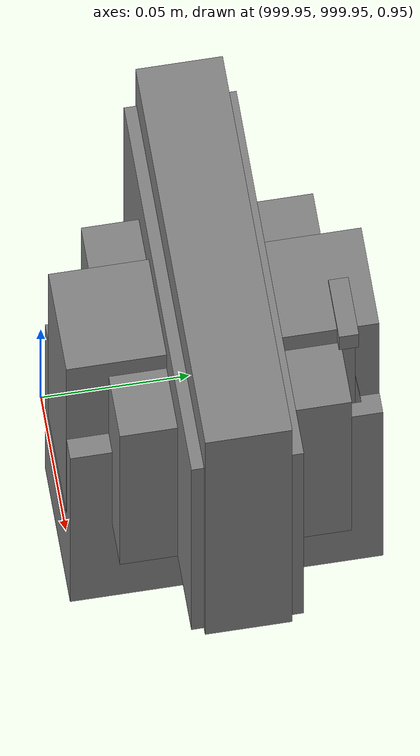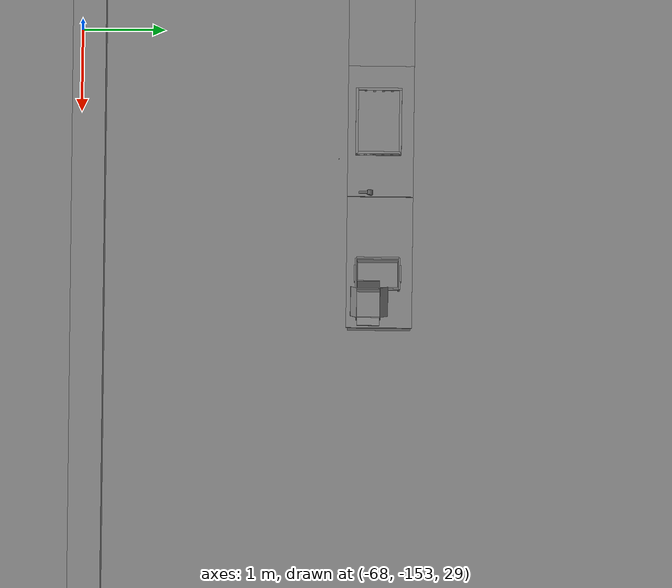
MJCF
<mujoco>
    <option gravity="0.000000000 0.000000000 -9.810000420" timestep="0.0049999999" integrator="implicitfast" density="1.225" viscosity="1.8000001e-05" noslip_iterations="10" iterations="100" sdf_iterations="50">
        <flag multiccd="disable"/>
    </option>
    <size memory="1000M"/>
    <compiler coordinate="local"/>
    <worldbody>
        <light cutoff="30" pos="0 1 1" dir="0 -1 -2"/>
        <light cutoff="30" pos="0 -1 1" dir="0 1 -2"/>
        <body pos="-64.866622925 -149.383972168 30.183746338" euler="89.999984741 89.999946594 0.000000000" name="openloong_gripper_2f85_fix_base_usda_bluebox_01">
            <geom contype="1" conaffinity="1" density="1000" type="box" material="" rgba="0.500000000 0.500000000 0.500000000 1.000000000" solimp="0.899999976 0.949999988 0.001000000" friction="1.000000000 0.005000000 0.000100000" solref="0.020000000 1.000000000" margin="0" condim="3" group="0" pos="0.276580811 0.187225342 0.000068665" quat="0.707106948 0.000077471 0.707106352 0.000077486" size="0.100000001 0.057999998 0.010000000" name="openloong_gripper_2f85_fix_base_usda_geom_3301531A_1911_48C2_A288_F98FB78D3429"/>
            <geom contype="1" conaffinity="1" density="1000" type="box" material="" rgba="0.500000000 0.500000000 0.500000000 1.000000000" solimp="0.899999976 0.949999988 0.001000000" friction="1.000000000 0.005000000 0.000100000" solref="0.020000000 1.000000000" margin="0" condim="3" group="0" pos="0.000000000 0.002883911 0.000000000" quat="0.999999881 0.000000000 0.000000000 0.000000000" size="0.254000008 0.003000000 0.172000006" name="openloong_gripper_2f85_fix_base_usda_geom_649D2DAA_5D8B_44A7_A7FA_36112B596E76"/>
            <geom contype="1" conaffinity="1" density="1000" type="box" material="" rgba="0.500000000 0.500000000 0.500000000 1.000000000" solimp="0.899999976 0.949999988 0.001000000" friction="1.000000000 0.005000000 0.000100000" solref="0.020000000 1.000000000" margin="0" condim="3" group="0" pos="0.000000000 0.124874115 0.173484802" quat="0.999796331 0.020176515 -0.000000015 0.000000030" size="0.259999990 0.119999997 0.007000000" name="openloong_gripper_2f85_fix_base_usda_geom_F0A5D81D_9926_49B4_95F1_2E0D91F017E1"/>
            <geom contype="1" conaffinity="1" density="1000" type="box" material="" rgba="0.500000000 0.500000000 0.500000000 1.000000000" solimp="0.899999976 0.949999988 0.001000000" friction="1.000000000 0.005000000 0.000100000" solref="0.020000000 1.000000000" margin="0" condim="3" group="0" pos="0.000000000 0.124874115 -0.173469543" quat="0.999796331 -0.020176545 -0.000000015 0.000000000" size="0.259999990 0.119999997 0.007000000" name="openloong_gripper_2f85_fix_base_usda_geom_98685ACD_169F_45B4_9A40_AC3943D02F4E"/>
            <geom contype="1" conaffinity="1" density="1000" type="box" material="" rgba="0.500000000 0.500000000 0.500000000 1.000000000" solimp="0.899999976 0.949999988 0.001000000" friction="1.000000000 0.005000000 0.000100000" solref="0.020000000 1.000000000" margin="0" condim="3" group="0" pos="0.000000000 0.214008331 0.188980103" quat="0.999912977 0.013176724 0.000000015 0.000000000" size="0.259999990 0.029999999 0.012500000" name="openloong_gripper_2f85_fix_base_usda_geom_140CCE45_3F56_4F24_B29E_820C55CA457E"/>
            <geom contype="1" conaffinity="1" density="1000" type="box" material="" rgba="0.500000000 0.500000000 0.500000000 1.000000000" solimp="0.899999976 0.949999988 0.001000000" friction="1.000000000 0.005000000 0.000100000" solref="0.020000000 1.000000000" margin="0" condim="3" group="0" pos="-0.258361816 0.125289917 0.001876831" quat="0.702796936 -0.020792112 0.710783124 0.020769298" size="0.189999998 0.119999997 0.009000000" name="openloong_gripper_2f85_fix_base_usda_geom_C6F98A95_0E9D_4E3D_BC68_FA651D7269C4"/>
            <geom contype="1" conaffinity="1" density="1000" type="box" material="" rgba="0.500000000 0.500000000 0.500000000 1.000000000" solimp="0.899999976 0.949999988 0.001000000" friction="1.000000000 0.005000000 0.000100000" solref="0.020000000 1.000000000" margin="0" condim="3" group="0" pos="0.000000000 0.214008331 -0.188980103" quat="0.999912977 -0.013176769 0.000000030 0.000000015" size="0.259999990 0.029999999 0.012500000" name="openloong_gripper_2f85_fix_base_usda_geom_BF6D24D9_A3BA_450D_9CEB_3B60292C1483"/>
            <geom contype="1" conaffinity="1" density="1000" type="box" material="" rgba="0.500000000 0.500000000 0.500000000 1.000000000" solimp="0.899999976 0.949999988 0.001000000" friction="1.000000000 0.005000000 0.000100000" solref="0.020000000 1.000000000" margin="0" condim="3" group="0" pos="-0.276611328 0.187225342 0.000068665" quat="0.707106650 0.000077441 0.707106709 0.000077456" size="0.100000001 0.057999998 0.010000000" name="openloong_gripper_2f85_fix_base_usda_geom_92781CFB_1823_414C_A98C_8883860D462D"/>
            <geom contype="1" conaffinity="1" density="1000" type="box" material="" rgba="0.500000000 0.500000000 0.500000000 1.000000000" solimp="0.899999976 0.949999988 0.001000000" friction="1.000000000 0.005000000 0.000100000" solref="0.020000000 1.000000000" margin="0" condim="3" group="0" pos="0.258331299 0.125289917 0.001876831" quat="0.702851415 0.018856421 0.710823774 -0.019329369" size="0.189999998 0.119999997 0.009000000" name="openloong_gripper_2f85_fix_base_usda_geom_45D7997D_06C6_4F02_B102_2F3C89BC068F"/>
            <freejoint name="openloong_gripper_2f85_fix_base_usda_bluebox_01_joint"/>
            <site size="0.005000000 0.005000000 0.005000000" rgba="0.500000000 0.500000000 0.500000000 1.000000000" pos="0.000000000 0.000000000 0.000000000" quat="0.999961913 0.008726534 0.000000000 0.000000000" group="0" type="sphere" name="openloong_gripper_2f85_fix_base_usda_bluebox_01site"/>
        </body>
        <body pos="-64.496299744 -149.491867065 30.235729218" euler="0.000000000 0.000000000 89.999946594" name="openloong_gripper_2f85_fix_base_usda_cardboardbox_01">
            <geom contype="1" conaffinity="1" density="1000" type="box" material="" rgba="0.500000000 0.500000000 0.500000000 1.000000000" solimp="0.899999976 0.949999988 0.001000000" friction="1.000000000 0.005000000 0.000100000" solref="0.020000000 1.000000000" margin="0" condim="3" group="0" pos="-0.003166199 -0.004086494 0.005052090" quat="1.000000000 0.000000000 0.000000000 0.000000000" size="0.142499998 0.177500010 0.005000000" name="openloong_gripper_2f85_fix_base_usda_geom_651BB00D_BB42_4DFC_AE43_22ECFB4B582D"/>
            <geom contype="1" conaffinity="1" density="1000" type="box" material="" rgba="0.500000000 0.500000000 0.500000000 1.000000000" solimp="0.899999976 0.949999988 0.001000000" friction="1.000000000 0.005000000 0.000100000" solref="0.020000000 1.000000000" margin="0" condim="3" group="0" pos="-0.003166199 0.170316696 0.150570869" quat="1.000000000 0.000000000 0.000000000 0.000000000" size="0.142499998 0.005000000 0.149999991" name="openloong_gripper_2f85_fix_base_usda_geom_E834B29E_C5D0_42CB_95E2_DBB52ACC4CFA"/>
            <geom contype="1" conaffinity="1" density="1000" type="box" material="" rgba="0.500000000 0.500000000 0.500000000 1.000000000" solimp="0.899999976 0.949999988 0.001000000" friction="1.000000000 0.005000000 0.000100000" solref="0.020000000 1.000000000" margin="0" condim="3" group="0" pos="-0.147399902 -0.005307198 0.150570869" quat="1.000000000 0.000000000 0.000000000 0.000000000" size="0.005000000 0.177500010 0.149999991" name="openloong_gripper_2f85_fix_base_usda_geom_7053E5C9_1119_4654_92DA_FBFA82D9A7AE"/>
            <geom contype="1" conaffinity="1" density="1000" type="box" material="" rgba="0.500000000 0.500000000 0.500000000 1.000000000" solimp="0.899999976 0.949999988 0.001000000" friction="1.000000000 0.005000000 0.000100000" solref="0.020000000 1.000000000" margin="0" condim="3" group="0" pos="0.140275955 -0.005307198 0.150570869" quat="1.000000000 0.000000000 0.000000000 0.000000000" size="0.005000000 0.177500010 0.149999991" name="openloong_gripper_2f85_fix_base_usda_geom_40311300_65FE_4C69_A1C4_9981C892B194"/>
            <geom contype="1" conaffinity="1" density="1000" type="box" material="" rgba="0.500000000 0.500000000 0.500000000 1.000000000" solimp="0.899999976 0.949999988 0.001000000" friction="1.000000000 0.005000000 0.000100000" solref="0.020000000 1.000000000" margin="0" condim="3" group="0" pos="-0.003166199 -0.181550980 0.150570869" quat="1.000000000 0.000000000 0.000000000 0.000000000" size="0.142499998 0.005000000 0.149999991" name="openloong_gripper_2f85_fix_base_usda_geom_A0B58C2A_AA8E_4BC9_8090_FA3FE38877E4"/>
            <freejoint name="openloong_gripper_2f85_fix_base_usda_cardboardbox_01_joint"/>
            <site size="0.005000000 0.005000000 0.005000000" rgba="0.500000000 0.500000000 0.500000000 1.000000000" pos="0.000000000 0.000000000 0.000000000" quat="0.999961913 0.008726535 0.000000000 0.000000000" group="0" type="sphere" name="openloong_gripper_2f85_fix_base_usda_site_5F8E5E53_4026_4B07_83D9_026D8DEFFD63"/>
            <body pos="0.139160156 -0.004048347 0.301930904" euler="-179.999954224 49.383502960 179.999954224" name="openloong_gripper_2f85_fix_base_usda_A1_006">
                <geom contype="1" conaffinity="1" density="1000" type="box" material="" rgba="0.500000000 0.500000000 0.500000000 1.000000000" solimp="0.899999976 0.949999988 0.001000000" friction="1.000000000 0.005000000 0.000100000" solref="0.020000000 1.000000000" margin="0" condim="3" group="0" pos="-0.071587563 0.000009537 0.001745224" quat="0.999999881 0.000000000 0.000000000 0.000000000" size="0.071249999 0.179999992 0.002500000" name="openloong_gripper_2f85_fix_base_usda_geom_94B87778_09CC_4F96_B64F_78F8772906CA"/>
                <joint armature="0" stiffness="0.07" damping="0.0099999998" axis="0.000000 1.000000 0.000000" type="hinge" name="openloong_gripper_2f85_fix_base_usda_A1_006"/>
            </body>
            <body pos="-0.145902634 -0.004086494 0.301938057" euler="-180.000000000 -60.000011444 -180.000000000" name="openloong_gripper_2f85_fix_base_usda_A2_006">
                <geom contype="1" conaffinity="1" density="1000" type="box" material="" rgba="0.500000000 0.500000000 0.500000000 1.000000000" solimp="0.899999976 0.949999988 0.001000000" friction="1.000000000 0.005000000 0.000100000" solref="0.020000000 1.000000000" margin="0" condim="3" group="0" pos="0.071268082 0.000009537 0.002717972" quat="0.000002921 0.000000000 -0.000000030 0.999999881" size="0.071249999 0.179999992 0.002500000" name="openloong_gripper_2f85_fix_base_usda_geom_91318F57_157E_4E68_89C4_0FF57D5345E7"/>
                <joint armature="0" stiffness="0.07" damping="0.0099999998" axis="0.000000 1.000000 0.000000" type="hinge" name="openloong_gripper_2f85_fix_base_usda_A2_006"/>
            </body>
            <body pos="-0.003385544 0.175991058 0.301930904" euler="-125.858116150 -0.000004561 0.000002331" name="openloong_gripper_2f85_fix_base_usda_B2_006">
                <geom contype="1" conaffinity="1" density="1000" type="box" material="" rgba="0.500000000 0.500000000 0.500000000 1.000000000" solimp="0.899999976 0.949999988 0.001000000" friction="1.000000000 0.005000000 0.000100000" solref="0.020000000 1.000000000" margin="0" condim="3" group="0" pos="0.000009537 -0.070939064 -0.002470016" quat="0.999614120 0.027776197 -0.000000015 0.000000030" size="0.137500003 0.064999998 0.005000000" name="openloong_gripper_2f85_fix_base_usda_geom_E8264676_BAD9_43B3_8382_91D94BF74A32"/>
                <joint armature="0" stiffness="0.07" damping="0.0099999998" axis="1.000000 0.000000 0.000000" type="hinge" name="openloong_gripper_2f85_fix_base_usda_B2_006"/>
            </body>
            <body pos="-0.003385544 -0.184140205 0.301938057" euler="147.805557251 0.000000000 0.000000000" name="openloong_gripper_2f85_fix_base_usda_B1_006">
                <geom contype="1" conaffinity="1" density="1000" type="box" material="" rgba="0.500000000 0.500000000 0.500000000 1.000000000" solimp="0.899999976 0.949999988 0.001000000" friction="1.000000000 0.005000000 0.000100000" solref="0.020000000 1.000000000" margin="0" condim="3" group="0" pos="-0.000028610 0.070202351 -0.002703667" quat="0.999614179 -0.027776167 0.000000000 0.000000000" size="0.137500003 0.064999998 0.005000000" name="openloong_gripper_2f85_fix_base_usda_geom_E0231571_BDC7_4A02_81F7_CF994E7B4637"/>
                <joint armature="0" stiffness="0.07" damping="0.0099999998" axis="1.000000 0.000000 0.000000" type="hinge" name="openloong_gripper_2f85_fix_base_usda_B1_006"/>
            </body>
        </body>
        <body pos="-65.882858276 -149.481979370 30.229999542" euler="-64.487716675 0.000000000 0.000000000" name="openloong_gripper_2f85_fix_base_usda_Barcode">
            <geom contype="1" conaffinity="1" density="1000" type="box" material="" rgba="0.500000000 0.500000000 0.500000000 1.000000000" solimp="0.899999976 0.949999988 0.001000000" friction="1.000000000 0.005000000 0.000100000" solref="0.020000000 1.000000000" margin="0" condim="3" group="0" pos="0.000000000 0.013038635 0.001419067" quat="0.000000000 0.000000000 0.000000000 1.000000119" size="0.034000002 0.010000000 0.017999999" name="openloong_gripper_2f85_fix_base_usda_geom_17E03A92_E079_4865_AD9D_6DE061E45F6B"/>
            <geom contype="1" conaffinity="1" density="1000" type="box" material="" rgba="0.500000000 0.500000000 0.500000000 1.000000000" solimp="0.899999976 0.949999988 0.001000000" friction="1.000000000 0.005000000 0.000100000" solref="0.020000000 1.000000000" margin="0" condim="3" group="0" pos="0.000000000 -0.035301208 -0.007095337" quat="0.000000000 0.000000000 -0.043619365 0.999048233" size="0.028999999 0.010000000 0.020000000" name="openloong_gripper_2f85_fix_base_usda_geom_F44DBA58_38C7_4481_BA7D_931EA1C29E0C"/>
            <geom contype="1" conaffinity="1" density="1000" type="box" material="" rgba="0.500000000 0.500000000 0.500000000 1.000000000" solimp="0.899999976 0.949999988 0.001000000" friction="1.000000000 0.005000000 0.000100000" solref="0.020000000 1.000000000" margin="0" condim="3" group="0" pos="0.000000000 -0.043411255 -0.011749268" quat="0.922262907 0.386563420 0.000000000 0.000000000" size="0.026000001 0.010000000 0.020000000" name="openloong_gripper_2f85_fix_base_usda_geom_B997DD20_1003_4004_ADD3_3F4EEDBEE53A"/>
            <geom contype="1" conaffinity="1" density="1000" type="box" material="" rgba="0.500000000 0.500000000 0.500000000 1.000000000" solimp="0.899999976 0.949999988 0.001000000" friction="1.000000000 0.005000000 0.000100000" solref="0.020000000 1.000000000" margin="0" condim="3" group="0" pos="0.000000000 -0.016967773 -0.031860352" quat="0.000000000 0.000000000 0.000000000 1.000000119" size="0.008000000 0.010000000 0.013000000" name="openloong_gripper_2f85_fix_base_usda_geom_51911065_5675_4F69_BD37_9D536BA6B6B0"/>
            <geom contype="1" conaffinity="1" density="1000" type="box" material="" rgba="0.500000000 0.500000000 0.500000000 1.000000000" solimp="0.899999976 0.949999988 0.001000000" friction="1.000000000 0.005000000 0.000100000" solref="0.020000000 1.000000000" margin="0" condim="3" group="0" pos="0.000000000 -0.001869202 0.000312805" quat="0.953716993 0.300705761 0.000000000 0.000000000" size="0.032000002 0.010000000 0.018999999" name="openloong_gripper_2f85_fix_base_usda_geom_9AD7D650_9997_4C0F_84F5_00B2DF21C3BA"/>
            <geom contype="1" conaffinity="1" density="1000" type="box" material="" rgba="0.500000000 0.500000000 0.500000000 1.000000000" solimp="0.899999976 0.949999988 0.001000000" friction="1.000000000 0.005000000 0.000100000" solref="0.020000000 1.000000000" margin="0" condim="3" group="0" pos="0.000000000 -0.019531250 -0.003173828" quat="0.953716993 0.300705761 0.000000000 0.000000000" size="0.030999999 0.010000000 0.020000000" name="openloong_gripper_2f85_fix_base_usda_geom_CB888458_C6B7_47FE_ABD7_9757635022FE"/>
            <geom contype="1" conaffinity="1" density="1000" type="box" material="" rgba="0.500000000 0.500000000 0.500000000 1.000000000" solimp="0.899999976 0.949999988 0.001000000" friction="1.000000000 0.005000000 0.000100000" solref="0.020000000 1.000000000" margin="0" condim="3" group="0" pos="0.000000000 -0.035301208 -0.007095337" quat="0.953716993 0.300705761 0.000000000 0.000000000" size="0.028999999 0.010000000 0.020000000" name="openloong_gripper_2f85_fix_base_usda_geom_C2AC257F_82A0_463B_89E1_7252AA18ABE5"/>
            <geom contype="1" conaffinity="1" density="1000" type="box" material="" rgba="0.500000000 0.500000000 0.500000000 1.000000000" solimp="0.899999976 0.949999988 0.001000000" friction="1.000000000 0.005000000 0.000100000" solref="0.020000000 1.000000000" margin="0" condim="3" group="0" pos="0.000000000 -0.042617798 -0.071121216" quat="0.000000000 0.000000000 0.000000000 1.000000119" size="0.013000000 0.021000000 0.059999999" name="openloong_gripper_2f85_fix_base_usda_geom_DCD7B654_A3A7_445D_9D8C_90AA75C572DE"/>
            <freejoint name="openloong_gripper_2f85_fix_base_usda_Barcode_joint"/>
            <site size="0.005000000 0.005000000 0.005000000" rgba="0.500000000 0.500000000 0.500000000 1.000000000" pos="0.000000000 0.000000000 0.000000000" quat="1.000000000 0.000000000 0.000000000 0.000000000" group="0" type="sphere" name="openloong_gripper_2f85_fix_base_usda_Barcode_site"/>
        </body>
        <body pos="-66.745018005 -149.392349243 30.184000015" euler="0.000000000 0.000000000 89.999946594" name="[22330633807622]_Basket_01">
            <geom contype="1" conaffinity="1" density="1000" type="box" material="" rgba="0.500000000 0.500000000 0.500000000 1.000000000" solimp="0.899999976 0.949999988 0.001000000" friction="1.000000000 0.005000000 0.000100000" solref="0.020000000 1.000000000" margin="0" condim="3" group="0" pos="-0.052425385 0.389207840 0.089787483" quat="0.707107008 0.000000000 0.000000000 0.707106411" size="0.014249999 0.014249999 0.059999999" name="[22330633807622]_geom_4386D7FA_DF80_48DC_BE1F_DDA75BBAF08C"/>
            <geom contype="1" conaffinity="1" density="1000" type="box" material="" rgba="0.500000000 0.500000000 0.500000000 1.000000000" solimp="0.899999976 0.949999988 0.001000000" friction="1.000000000 0.005000000 0.000100000" solref="0.020000000 1.000000000" margin="0" condim="3" group="0" pos="0.264015198 -0.133043289 0.089787483" quat="0.707107008 0.000000000 0.000000000 0.707106411" size="0.014249999 0.014249999 0.059999999" name="[22330633807622]_geom_89F28AE5_D3E8_46FF_BDD3_1FF79055C280"/>
            <geom contype="1" conaffinity="1" density="1000" type="box" material="" rgba="0.500000000 0.500000000 0.500000000 1.000000000" solimp="0.899999976 0.949999988 0.001000000" friction="1.000000000 0.005000000 0.000100000" solref="0.020000000 1.000000000" margin="0" condim="3" group="0" pos="-0.264015198 -0.265548706 0.089793205" quat="0.707107008 0.000000000 0.000000000 0.707106411" size="0.014249999 0.014249999 0.059999999" name="[22330633807622]_geom_BD3EA08E_53DC_4333_BEAC_295866D85D25"/>
            <geom contype="1" conaffinity="1" density="1000" type="box" material="" rgba="0.500000000 0.500000000 0.500000000 1.000000000" solimp="0.899999976 0.949999988 0.001000000" friction="1.000000000 0.005000000 0.000100000" solref="0.020000000 1.000000000" margin="0" condim="3" group="0" pos="-0.160263062 -0.389322281 0.089793205" quat="0.707107008 0.000000000 0.000000000 0.707106411" size="0.014249999 0.014249999 0.059999999" name="[22330633807622]_geom_3966849C_7C1C_4B5F_8550_6A4C6A0F4363"/>
            <geom contype="1" conaffinity="1" density="1000" type="box" material="" rgba="0.500000000 0.500000000 0.500000000 1.000000000" solimp="0.899999976 0.949999988 0.001000000" friction="1.000000000 0.005000000 0.000100000" solref="0.020000000 1.000000000" margin="0" condim="3" group="0" pos="0.162265778 -0.389322281 0.089787483" quat="0.707107008 0.000000000 0.000000000 0.707106411" size="0.014249999 0.014249999 0.059999999" name="[22330633807622]_geom_34CEE108_3772_4724_84E4_8B7BD182DE33"/>
            <geom contype="1" conaffinity="1" density="1000" type="box" material="" rgba="0.500000000 0.500000000 0.500000000 1.000000000" solimp="0.899999976 0.949999988 0.001000000" friction="1.000000000 0.005000000 0.000100000" solref="0.020000000 1.000000000" margin="0" condim="3" group="0" pos="0.264015198 0.389207840 0.089787483" quat="0.707107008 0.000000000 0.000000000 0.707106411" size="0.014249999 0.014249999 0.059999999" name="[22330633807622]_geom_F33967C6_1DF3_4573_92D9_875AE8532F89"/>
            <geom contype="1" conaffinity="1" density="1000" type="box" material="" rgba="0.500000000 0.500000000 0.500000000 1.000000000" solimp="0.899999976 0.949999988 0.001000000" friction="1.000000000 0.005000000 0.000100000" solref="0.020000000 1.000000000" margin="0" condim="3" group="0" pos="-0.264015198 -0.133043289 0.089793205" quat="0.707107008 0.000000000 0.000000000 0.707106411" size="0.014249999 0.014249999 0.059999999" name="[22330633807622]_geom_3BDE42FB_5752_4725_9270_BA09934CF25A"/>
            <geom contype="1" conaffinity="1" density="1000" type="box" material="" rgba="0.500000000 0.500000000 0.500000000 1.000000000" solimp="0.899999976 0.949999988 0.001000000" friction="1.000000000 0.005000000 0.000100000" solref="0.020000000 1.000000000" margin="0" condim="3" group="0" pos="-0.264026642 0.269256592 0.089793205" quat="0.707107008 0.000000000 0.000000000 0.707106411" size="0.014249999 0.014249999 0.059999999" name="[22330633807622]_geom_A3C3802E_4B90_4881_9940_3B3700027D34"/>
            <geom contype="1" conaffinity="1" density="1000" type="box" material="" rgba="0.500000000 0.500000000 0.500000000 1.000000000" solimp="0.899999976 0.949999988 0.001000000" friction="1.000000000 0.005000000 0.000100000" solref="0.020000000 1.000000000" margin="0" condim="3" group="0" pos="0.054462433 0.389207840 0.089787483" quat="0.707107008 0.000000000 0.000000000 0.707106411" size="0.014249999 0.014249999 0.059999999" name="[22330633807622]_geom_93F50937_E4C3_46BD_8DDB_6929E0D2F652"/>
            <geom contype="1" conaffinity="1" density="1000" type="box" material="" rgba="0.500000000 0.500000000 0.500000000 1.000000000" solimp="0.899999976 0.949999988 0.001000000" friction="1.000000000 0.005000000 0.000100000" solref="0.020000000 1.000000000" margin="0" condim="3" group="0" pos="0.054462433 -0.389322281 0.089787483" quat="0.707107008 0.000000000 0.000000000 0.707106411" size="0.014249999 0.014249999 0.059999999" name="[22330633807622]_geom_39DD3D2B_8E46_46B1_8807_AE6BB4D8DEC8"/>
            <geom contype="1" conaffinity="1" density="1000" type="box" material="" rgba="0.500000000 0.500000000 0.500000000 1.000000000" solimp="0.899999976 0.949999988 0.001000000" friction="1.000000000 0.005000000 0.000100000" solref="0.020000000 1.000000000" margin="0" condim="3" group="0" pos="0.264015198 0.269256592 0.089793205" quat="0.707107008 0.000000000 0.000000000 0.707106411" size="0.014249999 0.014249999 0.059999999" name="[22330633807622]_geom_D8139685_E23C_4D33_8314_9737091C4415"/>
            <geom contype="1" conaffinity="1" density="1000" type="box" material="" rgba="0.500000000 0.500000000 0.500000000 1.000000000" solimp="0.899999976 0.949999988 0.001000000" friction="1.000000000 0.005000000 0.000100000" solref="0.020000000 1.000000000" margin="0" condim="3" group="0" pos="0.264015198 -0.389322281 0.089787483" quat="0.707107008 0.000000000 0.000000000 0.707106411" size="0.014249999 0.014249999 0.059999999" name="[22330633807622]_geom_42533C90_E7A6_40A0_9DC5_4854F3FB0283"/>
            <geom contype="1" conaffinity="1" density="1000" type="box" material="" rgba="0.500000000 0.500000000 0.500000000 1.000000000" solimp="0.899999976 0.949999988 0.001000000" friction="1.000000000 0.005000000 0.000100000" solref="0.020000000 1.000000000" margin="0" condim="3" group="0" pos="0.000000000 0.000000000 0.015998840" quat="0.707107008 0.000000000 0.000000000 0.707106411" size="0.403499991 0.279000014 0.015750000" name="[22330633807622]_geom_D8C5E5A0_EC63_4C87_AE0E_F24E092C30A7"/>
            <geom contype="1" conaffinity="1" density="1000" type="box" material="" rgba="0.500000000 0.500000000 0.500000000 1.000000000" solimp="0.899999976 0.949999988 0.001000000" friction="1.000000000 0.005000000 0.000100000" solref="0.020000000 1.000000000" margin="0" condim="3" group="0" pos="0.000000000 -0.389476776 0.163619041" quat="0.707107008 0.000000000 0.000000000 0.707106411" size="0.015000000 0.277500004 0.015750000" name="[22330633807622]_geom_2A300DA5_7622_4833_8EA2_D95518BFAAB4"/>
            <geom contype="1" conaffinity="1" density="1000" type="box" material="" rgba="0.500000000 0.500000000 0.500000000 1.000000000" solimp="0.899999976 0.949999988 0.001000000" friction="1.000000000 0.005000000 0.000100000" solref="0.020000000 1.000000000" margin="0" condim="3" group="0" pos="0.162265778 0.389207840 0.089787483" quat="0.707107008 0.000000000 0.000000000 0.707106411" size="0.014249999 0.014249999 0.059999999" name="[22330633807622]_geom_58B58523_0007_4CA4_99CC_E058371B89C6"/>
            <geom contype="1" conaffinity="1" density="1000" type="box" material="" rgba="0.500000000 0.500000000 0.500000000 1.000000000" solimp="0.899999976 0.949999988 0.001000000" friction="1.000000000 0.005000000 0.000100000" solref="0.020000000 1.000000000" margin="0" condim="3" group="0" pos="0.000000000 0.389471054 0.163619041" quat="0.707107008 0.000000000 0.000000000 0.707106411" size="0.015000000 0.277500004 0.015750000" name="[22330633807622]_geom_4AF51E5F_EE3E_412A_9FAC_D9BBD15DA84E"/>
            <geom contype="1" conaffinity="1" density="1000" type="box" material="" rgba="0.500000000 0.500000000 0.500000000 1.000000000" solimp="0.899999976 0.949999988 0.001000000" friction="1.000000000 0.005000000 0.000100000" solref="0.020000000 1.000000000" margin="0" condim="3" group="0" pos="-0.263511658 0.000000000 0.163619041" quat="0.707107008 0.000000000 0.000000000 0.707106411" size="0.403499991 0.015000000 0.015750000" name="[22330633807622]_geom_FCF50DFA_5631_4AA6_BB46_5CFAEB45170D"/>
            <geom contype="1" conaffinity="1" density="1000" type="box" material="" rgba="0.500000000 0.500000000 0.500000000 1.000000000" solimp="0.899999976 0.949999988 0.001000000" friction="1.000000000 0.005000000 0.000100000" solref="0.020000000 1.000000000" margin="0" condim="3" group="0" pos="-0.264015198 0.141334534 0.089793205" quat="0.707107008 0.000000000 0.000000000 0.707106411" size="0.014249999 0.014249999 0.059999999" name="[22330633807622]_geom_4BC73FF0_DBCD_4559_8CD6_F81C9ACA9FB3"/>
            <geom contype="1" conaffinity="1" density="1000" type="box" material="" rgba="0.500000000 0.500000000 0.500000000 1.000000000" solimp="0.899999976 0.949999988 0.001000000" friction="1.000000000 0.005000000 0.000100000" solref="0.020000000 1.000000000" margin="0" condim="3" group="0" pos="0.264015198 -0.265548706 0.089787483" quat="0.707107008 0.000000000 0.000000000 0.707106411" size="0.014249999 0.014249999 0.059999999" name="[22330633807622]_geom_C5507406_CD2C_4E03_8C78_ABB6D89584F9"/>
            <geom contype="1" conaffinity="1" density="1000" type="box" material="" rgba="0.500000000 0.500000000 0.500000000 1.000000000" solimp="0.899999976 0.949999988 0.001000000" friction="1.000000000 0.005000000 0.000100000" solref="0.020000000 1.000000000" margin="0" condim="3" group="0" pos="-0.160263062 0.389207840 0.089787483" quat="0.707107008 0.000000000 0.000000000 0.707106411" size="0.014249999 0.014249999 0.059999999" name="[22330633807622]_geom_7EF229DC_6751_4FC9_B4D8_72CDD932DBE2"/>
            <geom contype="1" conaffinity="1" density="1000" type="box" material="" rgba="0.500000000 0.500000000 0.500000000 1.000000000" solimp="0.899999976 0.949999988 0.001000000" friction="1.000000000 0.005000000 0.000100000" solref="0.020000000 1.000000000" margin="0" condim="3" group="0" pos="-0.052425385 -0.389322281 0.089787483" quat="0.707107008 0.000000000 0.000000000 0.707106411" size="0.014249999 0.014249999 0.059999999" name="[22330633807622]_geom_3DDDFF84_5AC4_4CBC_8917_2AAC3C252C44"/>
            <geom contype="1" conaffinity="1" density="1000" type="box" material="" rgba="0.500000000 0.500000000 0.500000000 1.000000000" solimp="0.899999976 0.949999988 0.001000000" friction="1.000000000 0.005000000 0.000100000" solref="0.020000000 1.000000000" margin="0" condim="3" group="0" pos="-0.264026642 -0.389322281 0.089793205" quat="0.707107008 0.000000000 0.000000000 0.707106411" size="0.014249999 0.014249999 0.059999999" name="[22330633807622]_geom_B859CC96_0B48_4746_94CB_DFAE341770BD"/>
            <geom contype="1" conaffinity="1" density="1000" type="box" material="" rgba="0.500000000 0.500000000 0.500000000 1.000000000" solimp="0.899999976 0.949999988 0.001000000" friction="1.000000000 0.005000000 0.000100000" solref="0.020000000 1.000000000" margin="0" condim="3" group="0" pos="0.264015198 0.141334534 0.089787483" quat="0.707107008 0.000000000 0.000000000 0.707106411" size="0.014249999 0.014249999 0.059999999" name="[22330633807622]_geom_7EFEFA04_01AC_4A1D_B317_6D3CD0A5C90D"/>
            <geom contype="1" conaffinity="1" density="1000" type="box" material="" rgba="0.500000000 0.500000000 0.500000000 1.000000000" solimp="0.899999976 0.949999988 0.001000000" friction="1.000000000 0.005000000 0.000100000" solref="0.020000000 1.000000000" margin="0" condim="3" group="0" pos="-0.264015198 0.389207840 0.089793205" quat="0.707107008 0.000000000 0.000000000 0.707106411" size="0.014249999 0.014249999 0.059999999" name="[22330633807622]_geom_B1B08115_7659_48B7_A4F1_B6DEBA884017"/>
            <geom contype="1" conaffinity="1" density="1000" type="box" material="" rgba="0.500000000 0.500000000 0.500000000 1.000000000" solimp="0.899999976 0.949999988 0.001000000" friction="1.000000000 0.005000000 0.000100000" solref="0.020000000 1.000000000" margin="0" condim="3" group="0" pos="0.264015198 0.004480362 0.089787483" quat="0.707107008 0.000000000 0.000000000 0.707106411" size="0.014249999 0.014249999 0.059999999" name="[22330633807622]_geom_EC990934_162D_4948_9125_67A10B3F9F51"/>
            <geom contype="1" conaffinity="1" density="1000" type="box" material="" rgba="0.500000000 0.500000000 0.500000000 1.000000000" solimp="0.899999976 0.949999988 0.001000000" friction="1.000000000 0.005000000 0.000100000" solref="0.020000000 1.000000000" margin="0" condim="3" group="0" pos="0.263694763 -0.000011444 0.163619041" quat="0.707107008 0.000000000 0.000000000 0.707106411" size="0.403499991 0.015000000 0.015750000" name="[22330633807622]_geom_A8AA2FB2_9BFB_4EA4_AD2C_82E0342E7B38"/>
            <geom contype="1" conaffinity="1" density="1000" type="box" material="" rgba="0.500000000 0.500000000 0.500000000 1.000000000" solimp="0.899999976 0.949999988 0.001000000" friction="1.000000000 0.005000000 0.000100000" solref="0.020000000 1.000000000" margin="0" condim="3" group="0" pos="-0.264015198 0.004480362 0.089793205" quat="0.707107008 0.000000000 0.000000000 0.707106411" size="0.014249999 0.014249999 0.059999999" name="[22330633807622]_geom_72CEB8D7_3FD0_4958_B25E_1D8F7DD3DA96"/>
            <freejoint name="[22330633807622]_joint_A1A3D354_29D8_4988_BA1C_CACCDC4905C6"/>
        </body>
        <body pos="0.000000000 0.000000000 0.000000000" euler="0.000000000 0.000000000 0.000000000" name="Static Objects_Static Objects">
            <geom contype="1" conaffinity="1" density="1000" type="box" material="" rgba="0.500000000 0.500000000 0.500000000 1.000000000" solimp="0.899999976 0.949999988 0.001000000" friction="1.000000000 0.005000000 0.000100000" solref="0.020000000 1.000000000" margin="0" condim="3" group="0" pos="-67.544113159 -149.365814209 29.727830887" quat="0.500000417 0.499999970 0.499999553 0.499999970" size="0.381000012 0.319999993 0.041000001" name="Static Objects_geom_ED9961E4_C8F9_4AC3_98D0_728431117D6E"/>
            <geom contype="1" conaffinity="1" density="1000" type="box" material="" rgba="0.500000000 0.500000000 0.500000000 1.000000000" solimp="0.899999976 0.949999988 0.001000000" friction="1.000000000 0.005000000 0.000100000" solref="0.020000000 1.000000000" margin="0" condim="3" group="0" pos="-68.239501953 -149.365814209 30.086868286" quat="0.500000417 0.499999970 0.499999553 0.499999970" size="0.370999992 0.039500002 0.745000005" name="Static Objects_geom_D7C8136B_BDAF_4275_ACD6_3B1BEA37CF85"/>
            <geom contype="1" conaffinity="1" density="1000" type="box" material="" rgba="0.500000000 0.500000000 0.500000000 1.000000000" solimp="0.899999976 0.949999988 0.001000000" friction="1.000000000 0.005000000 0.000100000" solref="0.020000000 1.000000000" margin="0" condim="3" group="0" pos="-68.239501953 -149.365814209 30.147235870" quat="0.500000417 0.499999970 0.499999553 0.499999970" size="0.400000006 0.022000000 0.800000012" name="Static Objects_geom_50972568_BFBC_481B_9DC3_F0A76924F53F"/>
            <geom contype="1" conaffinity="1" density="1000" type="box" material="" rgba="0.500000000 0.500000000 0.500000000 1.000000000" solimp="0.899999976 0.949999988 0.001000000" friction="1.000000000 0.005000000 0.000100000" solref="0.020000000 1.000000000" margin="0" condim="3" group="0" pos="-68.934890747 -149.365814209 29.727830887" quat="0.500000417 0.499999970 0.499999553 0.499999970" size="0.381000012 0.319999993 0.041000001" name="Static Objects_geom_997C7CF7_68A7_4A1D_8B45_7F0504EF506C"/>
            <geom contype="1" conaffinity="1" density="1000" type="box" material="" rgba="0.500000000 0.500000000 0.500000000 1.000000000" solimp="0.899999976 0.949999988 0.001000000" friction="1.000000000 0.005000000 0.000100000" solref="0.020000000 1.000000000" margin="0" condim="3" group="0" pos="-68.239501953 -149.365814209 29.561563492" quat="0.500000417 0.499999970 0.499999553 0.499999970" size="0.020000000 0.022000000 0.660000026" name="Static Objects_geom_34C493D4_A7E5_455D_9A99_871C1B19C473"/>
            <geom contype="1" conaffinity="1" density="1000" type="box" material="" rgba="0.500000000 0.500000000 0.500000000 1.000000000" solimp="0.899999976 0.949999988 0.001000000" friction="1.000000000 0.005000000 0.000100000" solref="0.020000000 1.000000000" margin="0" condim="3" group="0" pos="-65.945671082 -149.365814209 29.727830887" quat="0.500000417 0.499999970 0.499999553 0.499999970" size="0.381000012 0.319999993 0.041000001" name="Static Objects_geom_4AFF874B_869A_4BF4_873A_84E9027CC2E3"/>
            <geom contype="1" conaffinity="1" density="1000" type="box" material="" rgba="0.500000000 0.500000000 0.500000000 1.000000000" solimp="0.899999976 0.949999988 0.001000000" friction="1.000000000 0.005000000 0.000100000" solref="0.020000000 1.000000000" margin="0" condim="3" group="0" pos="-66.641059875 -149.365814209 30.086868286" quat="0.500000417 0.499999970 0.499999553 0.499999970" size="0.370999992 0.039500002 0.745000005" name="Static Objects_geom_671286A1_A5A0_48A9_8EBF_89E6B1083DED"/>
            <geom contype="1" conaffinity="1" density="1000" type="box" material="" rgba="0.500000000 0.500000000 0.500000000 1.000000000" solimp="0.899999976 0.949999988 0.001000000" friction="1.000000000 0.005000000 0.000100000" solref="0.020000000 1.000000000" margin="0" condim="3" group="0" pos="-66.641059875 -149.365814209 30.147235870" quat="0.500000417 0.499999970 0.499999553 0.499999970" size="0.400000006 0.022000000 0.800000012" name="Static Objects_geom_ECEA3A9C_2407_4B51_AF68_B7E56FD006BB"/>
            <geom contype="1" conaffinity="1" density="1000" type="box" material="" rgba="0.500000000 0.500000000 0.500000000 1.000000000" solimp="0.899999976 0.949999988 0.001000000" friction="1.000000000 0.005000000 0.000100000" solref="0.020000000 1.000000000" margin="0" condim="3" group="0" pos="-67.336448669 -149.365814209 29.727830887" quat="0.500000417 0.499999970 0.499999553 0.499999970" size="0.381000012 0.319999993 0.041000001" name="Static Objects_geom_C086791F_E9C9_4423_929E_6C8A7B74F2BE"/>
            <geom contype="1" conaffinity="1" density="1000" type="box" material="" rgba="0.500000000 0.500000000 0.500000000 1.000000000" solimp="0.899999976 0.949999988 0.001000000" friction="1.000000000 0.005000000 0.000100000" solref="0.020000000 1.000000000" margin="0" condim="3" group="0" pos="-66.641059875 -149.365814209 29.561563492" quat="0.500000417 0.499999970 0.499999553 0.499999970" size="0.020000000 0.022000000 0.660000026" name="Static Objects_geom_7BF80BA2_70AD_4790_A2F5_B03BFFB06CC3"/>
            <geom contype="1" conaffinity="1" density="1000" type="box" material="" rgba="0.500000000 0.500000000 0.500000000 1.000000000" solimp="0.899999976 0.949999988 0.001000000" friction="1.000000000 0.005000000 0.000100000" solref="0.020000000 1.000000000" margin="0" condim="3" group="0" pos="-64.338577271 -149.365814209 29.727830887" quat="0.500000417 0.499999970 0.499999553 0.499999970" size="0.381000012 0.319999993 0.041000001" name="Static Objects_geom_ED1343A5_D9A3_431C_A0FB_57AB1278FA01"/>
            <geom contype="1" conaffinity="1" density="1000" type="box" material="" rgba="0.500000000 0.500000000 0.500000000 1.000000000" solimp="0.899999976 0.949999988 0.001000000" friction="1.000000000 0.005000000 0.000100000" solref="0.020000000 1.000000000" margin="0" condim="3" group="0" pos="-65.033966064 -149.365814209 30.086868286" quat="0.500000417 0.499999970 0.499999553 0.499999970" size="0.370999992 0.039500002 0.745000005" name="Static Objects_geom_C339FB67_90A3_446B_B30C_D0C7657C3953"/>
            <geom contype="1" conaffinity="1" density="1000" type="box" material="" rgba="0.500000000 0.500000000 0.500000000 1.000000000" solimp="0.899999976 0.949999988 0.001000000" friction="1.000000000 0.005000000 0.000100000" solref="0.020000000 1.000000000" margin="0" condim="3" group="0" pos="-65.033966064 -149.365814209 30.147235870" quat="0.500000417 0.499999970 0.499999553 0.499999970" size="0.400000006 0.022000000 0.800000012" name="Static Objects_geom_341C138E_E2D2_4BD7_8204_7B39FD96A171"/>
            <geom contype="1" conaffinity="1" density="1000" type="box" material="" rgba="0.500000000 0.500000000 0.500000000 1.000000000" solimp="0.899999976 0.949999988 0.001000000" friction="1.000000000 0.005000000 0.000100000" solref="0.020000000 1.000000000" margin="0" condim="3" group="0" pos="-65.729354858 -149.365814209 29.727830887" quat="0.500000417 0.499999970 0.499999553 0.499999970" size="0.381000012 0.319999993 0.041000001" name="Static Objects_geom_D3AC2BD2_4D23_47D2_BE2C_A625125C9BED"/>
            <geom contype="1" conaffinity="1" density="1000" type="box" material="" rgba="0.500000000 0.500000000 0.500000000 1.000000000" solimp="0.899999976 0.949999988 0.001000000" friction="1.000000000 0.005000000 0.000100000" solref="0.020000000 1.000000000" margin="0" condim="3" group="0" pos="-65.033966064 -149.365814209 29.561563492" quat="0.500000417 0.499999970 0.499999553 0.499999970" size="0.020000000 0.022000000 0.660000026" name="Static Objects_geom_FD844702_42B6_4946_B9A6_70E79768886C"/>
            <geom contype="1" conaffinity="1" density="1000" type="box" material="" rgba="0.500000000 0.500000000 0.500000000 1.000000000" solimp="0.899999976 0.949999988 0.001000000" friction="1.000000000 0.005000000 0.000100000" solref="0.020000000 1.000000000" margin="0" condim="3" group="0" pos="-61.754566193 -137.853729248 33.906845093" quat="0.707107067 0.000000000 0.000000000 0.707106471" size="0.759999990 0.759999990 4.500000000" name="Static Objects_geom_ED841095_F0AF_4BA8_8051_7E596A85F026"/>
            <geom contype="1" conaffinity="1" density="1000" type="box" material="" rgba="0.500000000 0.500000000 0.500000000 1.000000000" solimp="0.899999976 0.949999988 0.001000000" friction="1.000000000 0.005000000 0.000100000" solref="0.020000000 1.000000000" margin="0" condim="3" group="0" pos="-57.511135101 -144.927108765 31.707921982" quat="1.000000000 0.000000000 0.000000000 0.000000000" size="0.200000003 8.000000000 2.299999952" name="Static Objects_geom_34CA3BB0_298A_4F7C_B5FF_C5403BF490E2"/>
            <geom contype="1" conaffinity="1" density="1000" type="box" material="" rgba="0.500000000 0.500000000 0.500000000 1.000000000" solimp="0.899999976 0.949999988 0.001000000" friction="1.000000000 0.005000000 0.000100000" solref="0.020000000 1.000000000" margin="0" condim="3" group="0" pos="-80.517646790 -157.574050903 31.688196182" quat="0.707107067 0.000000000 0.000000000 0.707106471" size="0.600000024 0.600000024 2.299999952" name="Static Objects_geom_9CEF01C4_72AB_468F_968F_B80A505CEAD4"/>
            <geom contype="1" conaffinity="1" density="1000" type="box" material="" rgba="0.500000000 0.500000000 0.500000000 1.000000000" solimp="0.899999976 0.949999988 0.001000000" friction="1.000000000 0.005000000 0.000100000" solref="0.020000000 1.000000000" margin="0" condim="3" group="0" pos="-80.711044312 -147.414932251 31.666158676" quat="1.000000000 0.000000000 0.000000000 0.000000000" size="0.200000003 10.000000000 2.299999952" name="Static Objects_geom_E628F1FD_C144_4886_8680_5D11BF489DE0"/>
            <geom contype="1" conaffinity="1" density="1000" type="box" material="" rgba="0.500000000 0.500000000 0.500000000 1.000000000" solimp="0.899999976 0.949999988 0.001000000" friction="1.000000000 0.005000000 0.000100000" solref="0.020000000 1.000000000" margin="0" condim="3" group="0" pos="-57.687217712 -137.434692383 31.688196182" quat="0.707107067 0.000000000 0.000000000 0.707106471" size="0.600000024 0.600000024 2.299999952" name="Static Objects_geom_3FF6C459_488E_4CAD_B577_A2CB06DE1505"/>
            <geom contype="1" conaffinity="1" density="1000" type="box" material="" rgba="0.500000000 0.500000000 0.500000000 1.000000000" solimp="0.899999976 0.949999988 0.001000000" friction="1.000000000 0.005000000 0.000100000" solref="0.020000000 1.000000000" margin="0" condim="3" group="0" pos="-69.537033081 -140.263229370 31.714921951" quat="0.707107067 0.000000000 0.000000000 0.707106471" size="0.759999990 4.500000000 2.299999952" name="Static Objects_geom_AC7581A1_0D5A_4027_9B8B_B27B32A447DD"/>
            <geom contype="1" conaffinity="1" density="1000" type="box" material="" rgba="0.500000000 0.500000000 0.500000000 1.000000000" solimp="0.899999976 0.949999988 0.001000000" friction="1.000000000 0.005000000 0.000100000" solref="0.020000000 1.000000000" margin="0" condim="3" group="0" pos="-80.073638916 -137.853713989 33.906845093" quat="0.707107067 0.000000000 0.000000000 0.707106471" size="0.759999990 0.759999990 4.500000000" name="Static Objects_geom_93D84989_DD40_4A66_9C11_595434C43146"/>
            <geom contype="1" conaffinity="1" density="1000" type="box" material="" rgba="0.500000000 0.500000000 0.500000000 1.000000000" solimp="0.899999976 0.949999988 0.001000000" friction="1.000000000 0.005000000 0.000100000" solref="0.020000000 1.000000000" margin="0" condim="3" group="0" pos="-73.406707764 -155.734664917 31.707921982" quat="1.000000000 0.000000000 0.000000000 0.000000000" size="0.200000003 3.000000000 2.299999952" name="Static Objects_geom_AE3ADD06_E50D_4E35_A7E6_E80B92C9946D"/>
            <geom contype="1" conaffinity="1" density="1000" type="box" material="" rgba="0.500000000 0.500000000 0.500000000 1.000000000" solimp="0.899999976 0.949999988 0.001000000" friction="1.000000000 0.005000000 0.000100000" solref="0.020000000 1.000000000" margin="0" condim="3" group="0" pos="-68.497543335 -137.448257446 31.707921982" quat="0.707107067 0.000000000 0.000000000 0.707106471" size="0.200000003 14.000000000 2.299999952" name="Static Objects_geom_0C7C03F4_C83D_4C2F_98D8_21AE3D87237A"/>
            <geom contype="1" conaffinity="1" density="1000" type="cylinder" material="" rgba="0.500000000 0.500000000 0.500000000 1.000000000" solimp="0.899999976 0.949999988 0.001000000" friction="1.000000000 0.005000000 0.000100000" solref="0.020000000 1.000000000" margin="0" condim="3" group="0" pos="-68.868522644 -142.134506226 31.711090088" quat="0.707107067 0.000000000 0.000000000 0.707106471" size="0.509999990 2.299999952 1.000000000" name="Static Objects_geom_347903AC_5DC3_470F_87E0_04E927929448"/>
            <geom contype="1" conaffinity="1" density="1000" type="plane" material="" rgba="0.500000000 0.500000000 0.500000000 1.000000000" solimp="0.899999976 0.949999988 0.001000000" friction="1.000000000 0.005000000 0.000100000" solref="0.020000000 1.000000000" margin="0" condim="3" group="0" pos="-72.873703003 -147.131927490 29.409669876" quat="1.000000000 0.000000000 0.000000000 0.000000000" size="18.000000000 14.000000000 1.000000000" name="Static Objects_geom_8549000C_A828_4A4D_8A96_1EE5AAC9C93F"/>
            <geom contype="1" conaffinity="1" density="1000" type="box" material="" rgba="0.500000000 0.500000000 0.500000000 1.000000000" solimp="0.899999976 0.949999988 0.001000000" friction="1.000000000 0.005000000 0.000100000" solref="0.020000000 1.000000000" margin="0" condim="3" group="0" pos="-79.943580627 -157.782272339 31.707921982" quat="0.707107067 0.000000000 0.000000000 0.707106471" size="0.200000003 7.000000000 2.299999952" name="Static Objects_geom_DAB8FC26_BEA6_4E6F_A358_7D972D0D003B"/>
            <geom contype="1" conaffinity="1" density="1000" type="box" material="" rgba="0.500000000 0.500000000 0.500000000 1.000000000" solimp="0.899999976 0.949999988 0.001000000" friction="1.000000000 0.005000000 0.000100000" solref="0.020000000 1.000000000" margin="0" condim="3" group="0" pos="-65.421028137 -152.903442383 31.707921982" quat="0.707107067 0.000000000 0.000000000 0.707106471" size="0.200000003 7.800000191 2.299999952" name="Static Objects_geom_D04C4994_18B2_4183_97E4_B9A6E41B1AA8"/>
            <geom contype="1" conaffinity="1" density="1000" type="box" material="" rgba="0.500000000 0.500000000 0.500000000 1.000000000" solimp="0.899999976 0.949999988 0.001000000" friction="1.000000000 0.005000000 0.000100000" solref="0.020000000 1.000000000" margin="0" condim="3" group="0" pos="-74.776908875 -149.964416504 31.688196182" quat="1.000000000 0.000000000 0.000000000 0.000000000" size="0.600000024 0.409999996 2.299999952" name="Static Objects_geom_0F60AB15_3C57_4816_BB99_AA76BC3A85EC"/>
            <geom contype="1" conaffinity="1" density="1000" type="cylinder" material="" rgba="0.500000000 0.500000000 0.500000000 1.000000000" solimp="0.899999976 0.949999988 0.001000000" friction="1.000000000 0.005000000 0.000100000" solref="0.020000000 1.000000000" margin="0" condim="3" group="0" pos="-60.161884308 -142.134506226 31.711090088" quat="0.707107067 0.000000000 0.000000000 0.707106471" size="0.509999990 2.299999952 1.000000000" name="Static Objects_geom_FA577BBB_A8AB_4C77_9CEB_0A86E5914002"/>
            <geom contype="1" conaffinity="1" density="1000" type="cylinder" material="" rgba="0.500000000 0.500000000 0.500000000 1.000000000" solimp="0.899999976 0.949999988 0.001000000" friction="1.000000000 0.005000000 0.000100000" solref="0.020000000 1.000000000" margin="0" condim="3" group="0" pos="-75.382453918 -149.963455200 31.711090088" quat="0.707107067 0.000000000 0.000000000 0.707106471" size="0.409999996 2.299999952 1.000000000" name="Static Objects_geom_46D1AC49_34D0_4DB1_BC35_844E384A477C"/>
            <geom contype="1" conaffinity="1" density="1000" type="cylinder" material="" rgba="0.500000000 0.500000000 0.500000000 1.000000000" solimp="0.899999976 0.949999988 0.001000000" friction="1.000000000 0.005000000 0.000100000" solref="0.020000000 1.000000000" margin="0" condim="3" group="0" pos="-74.154960632 -149.963455200 31.711090088" quat="0.707107067 0.000000000 0.000000000 0.707106471" size="0.409999996 2.299999952 1.000000000" name="Static Objects_geom_9683B0C7_27A5_438B_B27E_6D13AE01C1D0"/>
            <geom contype="1" conaffinity="1" density="1000" type="cylinder" material="" rgba="0.500000000 0.500000000 0.500000000 1.000000000" solimp="0.899999976 0.949999988 0.001000000" friction="1.000000000 0.005000000 0.000100000" solref="0.020000000 1.000000000" margin="0" condim="3" group="0" pos="-77.566612244 -142.134506226 31.711090088" quat="0.707107067 0.000000000 0.000000000 0.707106471" size="0.509999990 2.299999952 1.000000000" name="Static Objects_geom_ECD1AD15_85C1_4C56_904A_3CC2EB601652"/>
        </body>
        <body pos="-65.898483276 -148.977203369 31.169237137" euler="-153.370010376 -85.289184570 140.576965332" mocap="true" name="spotlight4_SpotLight"/>
        <body pos="1000.000000000 1000.000000000 1.000000000" euler="0.000000000 0.000000000 180.000000000" name="openloong_gripper_2f85_fix_base_usda_battery_01">
            <geom contype="1" conaffinity="1" density="1000" type="box" material="" rgba="0.500000000 0.500000000 0.500000000 1.000000000" solimp="0.899999976 0.949999988 0.001000000" friction="1.000000000 0.005000000 0.000100000" solref="0.020000000 1.000000000" margin="0" condim="3" group="0" pos="-0.011123657 -0.041940309 0.101691343" quat="1.000000000 0.000000000 0.000000000 0.000000000" size="0.010800000 0.003375000 0.004725000" name="openloong_gripper_2f85_fix_base_usda_geom_8AF3F140_D36B_44CF_BA01_5B10539F8664"/>
            <geom contype="1" conaffinity="1" density="1000" type="box" material="" rgba="0.500000000 0.500000000 0.500000000 1.000000000" solimp="0.899999976 0.949999988 0.001000000" friction="1.000000000 0.005000000 0.000100000" solref="0.020000000 1.000000000" margin="0" condim="3" group="0" pos="-0.010876465 -0.044247437 0.047066893" quat="0.998702705 -0.050920475 0.000000000 0.000000000" size="0.009450001 0.002700000 0.024975000" name="openloong_gripper_2f85_fix_base_usda_geom_407DFBCD_A1B7_466B_B7A9_2D884392D381"/>
            <geom contype="1" conaffinity="1" density="1000" type="box" material="" rgba="0.500000000 0.500000000 0.500000000 1.000000000" solimp="0.899999976 0.949999988 0.001000000" friction="1.000000000 0.005000000 0.000100000" solref="0.020000000 1.000000000" margin="0" condim="3" group="0" pos="-0.001235962 -0.000659180 0.047381196" quat="1.000000000 0.000000000 0.000000000 0.000000000" size="0.039420001 0.039150000 0.047250003" name="openloong_gripper_2f85_fix_base_usda_geom_08D2E108_BDAF_4C20_9F6B_AB835165F2DC"/>
            <geom contype="1" conaffinity="1" density="1000" type="box" material="" rgba="0.500000000 0.500000000 0.500000000 1.000000000" solimp="0.899999976 0.949999988 0.001000000" friction="1.000000000 0.005000000 0.000100000" solref="0.020000000 1.000000000" margin="0" condim="3" group="0" pos="-0.010876465 -0.039138794 0.009851727" quat="1.000000000 0.000000000 0.000000000 0.000000000" size="0.009450001 0.010800000 0.013500000" name="openloong_gripper_2f85_fix_base_usda_geom_BB190056_BF42_4369_88A1_A879F9BC0406"/>
            <geom contype="1" conaffinity="1" density="1000" type="box" material="" rgba="0.500000000 0.500000000 0.500000000 1.000000000" solimp="0.899999976 0.949999988 0.001000000" friction="1.000000000 0.005000000 0.000100000" solref="0.020000000 1.000000000" margin="0" condim="3" group="0" pos="-0.010876465 -0.041528322 0.071508206" quat="1.000000000 0.000000000 0.000000000 0.000000000" size="0.009450001 0.002700000 0.027000001" name="openloong_gripper_2f85_fix_base_usda_geom_9EFE8B49_8545_455A_9D51_DA5F7F352EC5"/>
            <freejoint name="openloong_gripper_2f85_fix_base_usda_battery_01_joint"/>
            <site size="0.005000000 0.005000000 0.005000000" rgba="0.500000000 0.500000000 0.500000000 1.000000000" pos="0.000000000 0.000000000 0.000000000" quat="0.999961913 0.008726500 0.000000000 0.000000000" group="0" type="sphere" name="openloong_gripper_2f85_fix_base_usda_battery_01site"/>
        </body>
        <body pos="1000.000000000 1000.000000000 1.000000000" euler="0.000000000 0.000000000 180.000000000" name="openloong_gripper_2f85_fix_base_usda_cpu_fan">
            <geom contype="1" conaffinity="1" density="1000" type="box" material="" rgba="0.500000000 0.500000000 0.500000000 1.000000000" solimp="0.899999976 0.949999988 0.001000000" friction="1.000000000 0.005000000 0.000100000" solref="0.020000000 1.000000000" margin="0" condim="3" group="0" pos="0.000000000 0.000000000 0.070034981" quat="0.000000000 0.000000000 0.000000000 1.000000000" size="0.070700005 0.014699999 0.070700005" name="openloong_gripper_2f85_fix_base_usda_geom_912B8D94_BD70_4776_B47D_A3544509012C"/>
            <freejoint name="openloong_gripper_2f85_fix_base_usda_cpu_fan_joint"/>
            <site size="0.005000000 0.005000000 0.005000000" rgba="0.500000000 0.500000000 0.500000000 1.000000000" pos="0.000000000 0.000000000 0.000000000" quat="0.999961913 0.008726535 0.000000000 0.000000000" group="0" type="sphere" name="openloong_gripper_2f85_fix_base_usda_cpu_fancsite"/>
        </body>
        <body pos="1000.000000000 1000.000000000 1.000000000" euler="0.000000000 0.000000000 180.000000000" name="openloong_gripper_2f85_fix_base_usda_wifi_box">
            <geom contype="1" conaffinity="1" density="1000" type="box" material="" rgba="0.500000000 0.500000000 0.500000000 1.000000000" solimp="0.899999976 0.949999988 0.001000000" friction="1.000000000 0.005000000 0.000100000" solref="0.020000000 1.000000000" margin="0" condim="3" group="0" pos="0.000000000 0.000000000 0.058978677" quat="0.000000000 0.000000047 0.000000000 1.000000000" size="0.068499997 0.018999999 0.059000000" name="openloong_gripper_2f85_fix_base_usda_geom_4B62EE06_F1FC_45D9_9DA2_51DCF6662823"/>
            <freejoint name="openloong_gripper_2f85_fix_base_usda_wifi_box_joint"/>
            <site size="0.005000000 0.005000000 0.005000000" rgba="0.500000000 0.500000000 0.500000000 1.000000000" pos="0.000000000 0.000000000 0.000000000" quat="0.999961913 0.008726500 0.000000000 0.000000000" group="0" type="sphere" name="openloong_gripper_2f85_fix_base_usda_wifi_boxsite"/>
        </body>
        <body pos="-66.389198303 -149.770004272 31.162155151" euler="-157.663436890 21.740867615 -141.753417969" mocap="true" name="spotlight6_SpotLight"/>
        <body pos="1000.000000000 1000.000000000 1.000000000" euler="0.000011953 0.000005123 -179.999984741" name="openloong_gripper_2f85_fix_base_usda_intel_box">
            <geom contype="1" conaffinity="1" density="1000" type="box" material="" rgba="0.500000000 0.500000000 0.500000000 1.000000000" solimp="0.899999976 0.949999988 0.001000000" friction="1.000000000 0.005000000 0.000100000" solref="0.020000000 1.000000000" margin="0" condim="3" group="0" pos="0.000000000 -0.000067139 0.000082284" quat="0.707106709 0.000000225 0.000000253 0.707106650" size="0.052800003 0.025300000 0.052800003" name="openloong_gripper_2f85_fix_base_usda_geom_B10A26D4_F86B_44E4_93C8_7291948F1AE3"/>
            <freejoint name="openloong_gripper_2f85_fix_base_usda_intel_box_joint"/>
            <site size="0.005000000 0.005000000 0.005000000" rgba="0.500000000 0.500000000 0.500000000 1.000000000" pos="0.000000000 0.000000000 0.000000000" quat="0.999961913 0.008726500 0.000000000 0.000000000" group="0" type="sphere" name="openloong_gripper_2f85_fix_base_usda_intel_boxsite"/>
        </body>
        <body pos="1000.000000000 999.999938965 1.000000000" euler="0.000000000 0.000000000 180.000000000" name="openloong_gripper_2f85_fix_base_usda_intelcore_i5">
            <geom contype="1" conaffinity="1" density="1000" type="box" material="" rgba="0.500000000 0.500000000 0.500000000 1.000000000" solimp="0.899999976 0.949999988 0.001000000" friction="1.000000000 0.005000000 0.000100000" solref="0.020000000 1.000000000" margin="0" condim="3" group="0" pos="0.000000000 0.000000000 0.051722717" quat="0.707106709 0.000000000 0.000000000 -0.707106769" size="0.052800000 0.018080002 0.052800000" name="openloong_gripper_2f85_fix_base_usda_geom_9119CE9B_5C83_4FF5_A910_C792027A0DF9"/>
            <freejoint name="openloong_gripper_2f85_fix_base_usda_intelcore_i5_joint"/>
            <site size="0.005000000 0.005000000 0.005000000" rgba="0.500000000 0.500000000 0.500000000 1.000000000" pos="0.000000000 0.000000000 0.000000000" quat="0.999961913 0.008726534 0.000000000 0.000000000" group="0" type="sphere" name="openloong_gripper_2f85_fix_base_usda_intelcore_i5site"/>
        </body>
        <body pos="-66.044075012 -149.339614868 31.168760300" euler="176.832199097 3.006125689 118.662620544" mocap="true" name="spotlight2_SpotLight"/>
        <body pos="-66.291030884 -149.869689941 29.018842697" euler="0.000000000 0.000000000 89.999946594" mocap="true" name="openloong_gripper_2f85_fix_base_usda_leftHandMocap"/>
        <body pos="-66.291030884 -149.869689941 29.018842697" euler="0.000000000 0.000000000 89.999946594" mocap="true" name="openloong_gripper_2f85_fix_base_usda_rightHandMocap"/>
        <body pos="-66.291030884 -149.869689941 30.218843460" euler="0.000000000 0.000000000 89.999946594" name="openloong_gripper_2f85_fix_base_usda_base_link">
            <geom contype="1" conaffinity="1" density="1000" type="mesh" material="" rgba="0.783999979 0.783999979 0.783999979 1.000000000" solimp="0.899999976 0.949999988 0.001000000" friction="1.000000000 0.005000000 0.000100000" solref="0.020000000 1.000000000" margin="0" condim="3" group="3" mesh="base_link" pos="0.000000000 0.000000000 0.000000000" quat="1.000000000 0.000000000 0.000000000 0.000000000" size="1.000000000 1.000000000 1.000000000" name="openloong_gripper_2f85_fix_base_usda__geom_7_01C9FAA8_B4CD_4A93_B4A3_DD6256A16194"/>
            <site size="0.005000000 0.005000000 0.005000000" rgba="0.500000000 0.500000000 0.500000000 1.000000000" pos="0.000000000 0.000000000 0.000000000" quat="1.000000000 0.000000000 0.000000000 0.000000000" group="0" type="sphere" name="openloong_gripper_2f85_fix_base_usda_imu"/>
            <inertial mass="22.447001" pos="-0.005664100 -0.001336700 0.238289997" diaginertia="0.374352545 0.277180195 0.220617250" quat="0.999247074 0.035235517 -0.015086859 0.006023135"/>
            <body pos="0.000000000 0.000000000 0.299997330" euler="0.000000000 0.000000000 0.000000000" name="openloong_gripper_2f85_fix_base_usda_dummy_body">
                <geom contype="1" conaffinity="1" density="1000" type="sphere" material="" rgba="0.783999979 0.783999979 0.783999979 1.000000000" solimp="0.899999976 0.949999988 0.001000000" friction="1.000000000 0.005000000 0.000100000" solref="0.020000000 1.000000000" margin="0" condim="3" group="3" pos="0.000000000 0.000000000 0.000000000" quat="1.000000000 0.000000000 0.000000000 0.000000000" size="0.010000000 0.000000000 0.000000000" name="openloong_gripper_2f85_fix_base_usda__geom_8_0D516C00_3280_4992_8134_DBEDFD57F111"/>
                <joint armature="0.0099999998" stiffness="0" damping="0.1" axis="0.000000 0.000000 1.000000" type="hinge" name="openloong_gripper_2f85_fix_base_usda_dummy_joint"/>
                <site size="0.010000000 0.005000000 0.005000000" rgba="0.500000000 0.500000000 0.500000000 1.000000000" pos="0.000000000 0.000000000 0.000000000" quat="1.000000000 0.000000000 0.000000000 0.000000000" group="3" type="sphere" name="openloong_gripper_2f85_fix_base_usda_dummy_site"/>
            </body>
            <body pos="0.009002686 0.000000000 0.406400681" euler="0.000000000 0.000000000 0.000000000" name="openloong_gripper_2f85_fix_base_usda_Link_head_yaw">
                <geom contype="1" conaffinity="1" density="1000" type="mesh" material="" rgba="0.783999979 0.783999979 0.783999979 1.000000000" solimp="0.899999976 0.949999988 0.001000000" friction="1.000000000 0.005000000 0.000100000" solref="0.020000000 1.000000000" margin="0" condim="3" group="3" mesh="Link_head_yaw" pos="0.000000000 0.000000000 0.000000000" quat="1.000000000 0.000000000 0.000000000 0.000000000" size="1.000000000 1.000000000 1.000000000" name="openloong_gripper_2f85_fix_base_usda__geom_10_2418BAD4_670C_49B4_8E13_211DE9E23EA5"/>
                <inertial mass="0.84249002" pos="0.000000000 -0.002081400 0.044801001" diaginertia="0.000700588 0.000629000 0.000553812" quat="0.706933022 -0.015675601 0.015677100 0.706933022"/>
                <body pos="0.000000000 -0.034599304 0.048500061" euler="0.000000000 0.000000000 0.000000000" name="openloong_gripper_2f85_fix_base_usda_Link_head_pitch">
                    <geom contype="1" conaffinity="1" density="1000" type="mesh" material="" rgba="0.783999979 0.783999979 0.783999979 1.000000000" solimp="0.899999976 0.949999988 0.001000000" friction="1.000000000 0.005000000 0.000100000" solref="0.020000000 1.000000000" margin="0" condim="3" group="3" mesh="Link_head_pitch" pos="0.000000000 0.000000000 0.000000000" quat="1.000000000 0.000000000 0.000000000 0.000000000" size="1.000000000 1.000000000 1.000000000" name="openloong_gripper_2f85_fix_base_usda__geom_12_DEFA9E7C_F311_4EC9_8E3E_A583D5236680"/>
                    <inertial mass="1.3943" pos="0.020569000 0.033004001 0.125000000" diaginertia="0.006381400 0.006289940 0.004481460" quat="0.973390222 0.008406822 0.228157058 0.019624906"/>
                    <body pos="0.000000000 0.029998779 0.000000000" euler="0.000000000 0.000000000 0.000000000" name="openloong_gripper_2f85_fix_base_usda_neck_center_body">
                        <site size="0.010000000 0.005000000 0.005000000" rgba="0.500000000 0.500000000 0.500000000 1.000000000" pos="0.000000000 0.000000000 0.000000000" quat="1.000000000 0.000000000 0.000000000 0.000000000" group="3" type="sphere" name="openloong_gripper_2f85_fix_base_usda_neck_center_site"/>
                        <body pos="0.020004272 0.000000000 0.149999619" euler="-0.000002229 39.998176575 -90.000205994" name="openloong_gripper_2f85_fix_base_usda_camera_head">
                            <site size="0.010000000 0.005000000 0.005000000" rgba="0.500000000 0.500000000 0.500000000 1.000000000" pos="0.000000000 0.000000000 0.000000000" quat="1.000000000 0.000000000 0.000000000 0.000000000" group="3" type="sphere" name="openloong_gripper_2f85_fix_base_usda_camera_head_site"/>
                        </body>
                    </body>
                </body>
            </body>
            <body pos="0.003997803 -0.161598206 0.392200470" euler="0.000000000 0.000000000 0.000000000" name="openloong_gripper_2f85_fix_base_usda_Link_arm_r_01">
                <geom contype="1" conaffinity="1" density="1000" type="mesh" material="" rgba="0.783999979 0.783999979 0.783999979 1.000000000" solimp="0.899999976 0.949999988 0.001000000" friction="1.000000000 0.005000000 0.000100000" solref="0.020000000 1.000000000" margin="0" condim="3" group="3" mesh="Link_arm_r_01" pos="0.000000000 0.000000000 0.000000000" quat="1.000000000 0.000000000 0.000000000 0.000000000" size="1.000000000 1.000000000 1.000000000" name="openloong_gripper_2f85_fix_base_usda__geom_14_41344336_77BF_487A_B69E_74EEEB98E9C6"/>
                <joint armature="0.0099999998" stiffness="0" damping="1" axis="0.000000 -1.000000 0.000000" limited="true" range="-170.000015259 170.000015259" type="hinge" name="openloong_gripper_2f85_fix_base_usda_J_arm_r_01"/>
                <inertial mass="0.75641" pos="0.004494600 -0.038293999 -0.000001874" diaginertia="0.000842990 0.000803050 0.000587120" quat="-0.000163502 0.707098067 0.000812463 0.707115054"/>
                <body pos="-0.041992188 -0.041000366 0.000000000" euler="0.000000000 0.000000000 0.000000000" name="openloong_gripper_2f85_fix_base_usda_Link_arm_r_02">
                    <geom contype="1" conaffinity="1" density="1000" type="mesh" material="" rgba="0.783999979 0.783999979 0.783999979 1.000000000" solimp="0.899999976 0.949999988 0.001000000" friction="1.000000000 0.005000000 0.000100000" solref="0.020000000 1.000000000" margin="0" condim="3" group="3" mesh="Link_arm_r_02" pos="0.000000000 0.000000000 0.000000000" quat="1.000000000 0.000000000 0.000000000 0.000000000" size="1.000000000 1.000000000 1.000000000" name="openloong_gripper_2f85_fix_base_usda__geom_16_95AC25D5_3CC7_479C_A87A_508465FFA46B"/>
                    <joint armature="0.0099999998" stiffness="0" damping="1" axis="-1.000000 0.000000 0.000000" limited="true" range="-105.000244141 105.000244141" type="hinge" name="openloong_gripper_2f85_fix_base_usda_J_arm_r_02"/>
                    <inertial mass="0.98500001" pos="0.041999999 -0.067430697 0.000000000" diaginertia="0.002262690 0.001730990 0.001154020" quat="0.500000000 0.500000000 -0.500000000 0.500000000"/>
                    <body pos="0.041992188 -0.122596741 0.000000000" euler="0.000000000 0.000000000 0.000000000" name="openloong_gripper_2f85_fix_base_usda_Link_arm_r_03">
                        <geom contype="1" conaffinity="1" density="1000" type="mesh" material="" rgba="0.783999979 0.783999979 0.783999979 1.000000000" solimp="0.899999976 0.949999988 0.001000000" friction="1.000000000 0.005000000 0.000100000" solref="0.020000000 1.000000000" margin="0" condim="3" group="3" mesh="Link_arm_r_03" pos="0.000000000 0.000000000 0.000000000" quat="1.000000000 0.000000000 0.000000000 0.000000000" size="1.000000000 1.000000000 1.000000000" name="openloong_gripper_2f85_fix_base_usda__geom_18_7C285284_F3BD_4FAD_A216_63BE7C2E5BA0"/>
                        <joint armature="0.0099999998" stiffness="0" damping="1" axis="0.000000 -1.000000 0.000000" limited="true" range="-170.000015259 170.000015259" type="hinge" name="openloong_gripper_2f85_fix_base_usda_J_arm_r_03"/>
                        <inertial mass="0.95899999" pos="-0.001413580 -0.164663002 0.020757901" diaginertia="0.002101340 0.002064590 0.000754802" quat="0.560480952 0.454391927 -0.443732947 0.531497955"/>
                        <body pos="0.035293579 -0.177406311 0.023998260" euler="0.000000000 0.000000000 0.000000000" name="openloong_gripper_2f85_fix_base_usda_Link_arm_r_04">
                            <geom contype="1" conaffinity="1" density="1000" type="mesh" material="" rgba="0.783999979 0.783999979 0.783999979 1.000000000" solimp="0.899999976 0.949999988 0.001000000" friction="1.000000000 0.005000000 0.000100000" solref="0.020000000 1.000000000" margin="0" condim="3" group="3" mesh="Link_arm_r_04" pos="0.000000000 0.000000000 0.000000000" quat="1.000000000 0.000000000 0.000000000 0.000000000" size="1.000000000 1.000000000 1.000000000" name="openloong_gripper_2f85_fix_base_usda__geom_20_A6EF24B1_3637_4C81_A915_F2BD04C18393"/>
                            <joint armature="0.0099999998" stiffness="0" damping="1" axis="-1.000000 0.000000 0.000000" limited="true" range="0.000000000 170.000015259" type="hinge" name="openloong_gripper_2f85_fix_base_usda_J_arm_r_04"/>
                            <inertial mass="0.60000002" pos="-0.038727000 -0.060766999 -0.021003000" diaginertia="0.001092610 0.000712422 0.000645102" quat="0.327701002 0.632602990 -0.467366993 0.523443997"/>
                            <body pos="-0.035293579 -0.103492737 -0.023998260" euler="0.000000000 0.000000000 0.000000000" name="openloong_gripper_2f85_fix_base_usda_Link_arm_r_05">
                                <geom contype="1" conaffinity="1" density="1000" type="mesh" material="" rgba="0.783999979 0.783999979 0.783999979 1.000000000" solimp="0.899999976 0.949999988 0.001000000" friction="1.000000000 0.005000000 0.000100000" solref="0.020000000 1.000000000" margin="0" condim="3" group="3" mesh="Link_arm_r_05" pos="0.000000000 0.000000000 0.000000000" quat="1.000000000 0.000000000 0.000000000 0.000000000" size="1.000000000 1.000000000 1.000000000" name="openloong_gripper_2f85_fix_base_usda__geom_22_CF5DA966_BB98_4434_80A0_713DC6F25782"/>
                                <joint armature="0.0099999998" stiffness="0" damping="1" axis="0.000000 -1.000000 0.000000" limited="true" range="-170.000015259 170.000015259" type="hinge" name="openloong_gripper_2f85_fix_base_usda_J_arm_r_05"/>
                                <inertial mass="0.68976003" pos="0.000032712 -0.068658002 -0.000111780" diaginertia="0.002522510 0.002411100 0.000448695" quat="0.707660973 0.706543028 -0.002603360 0.002470550"/>
                                <body pos="-0.026489258 -0.196502686 0.000000000" euler="0.000000000 0.000000000 0.000000000" name="openloong_gripper_2f85_fix_base_usda_Link_arm_r_06">
                                    <geom contype="1" conaffinity="1" density="1000" type="mesh" material="" rgba="0.783999979 0.783999979 0.783999979 1.000000000" solimp="0.899999976 0.949999988 0.001000000" friction="1.000000000 0.005000000 0.000100000" solref="0.020000000 1.000000000" margin="0" condim="3" group="3" mesh="Link_arm_r_06" pos="0.000000000 0.000000000 0.000000000" quat="1.000000000 0.000000000 0.000000000 0.000000000" size="1.000000000 1.000000000 1.000000000" name="openloong_gripper_2f85_fix_base_usda__geom_24_03FB4D4D_5A27_45B0_9C16_498133F88915"/>
                                    <joint armature="0.0099999998" stiffness="0" damping="1" axis="1.000000 0.000000 0.000000" limited="true" range="-105.000244141 105.000244141" type="hinge" name="openloong_gripper_2f85_fix_base_usda_J_arm_r_06"/>
                                    <inertial mass="0.28" pos="0.026078001 -0.000000896 0.001663700" diaginertia="0.000156930 0.000145601 0.000104979" quat="0.707080841 0.001851080 0.001883810 0.707127810"/>
                                    <body pos="0.026489258 0.000000000 0.031799316" euler="0.000000000 0.000000000 0.000000000" name="openloong_gripper_2f85_fix_base_usda_Link_arm_r_07">
                                        <geom contype="1" conaffinity="1" density="1000" type="mesh" material="" rgba="0.783999979 0.783999979 0.783999979 1.000000000" solimp="0.899999976 0.949999988 0.001000000" friction="1.000000000 0.005000000 0.000100000" solref="0.020000000 1.000000000" margin="0" condim="3" group="3" mesh="Link_arm_r_07" pos="0.000000000 0.000000000 0.000000000" quat="1.000000000 0.000000000 0.000000000 0.000000000" size="1.000000000 1.000000000 1.000000000" name="openloong_gripper_2f85_fix_base_usda__geom_26_93D416EA_DD2D_4AA7_9FAB_A71CAAFBD887"/>
                                        <joint armature="0.0099999998" stiffness="0" damping="1" axis="0.000000 0.000000 1.000000" limited="true" range="-60.000133514 60.000133514" type="hinge" name="openloong_gripper_2f85_fix_base_usda_J_arm_r_07"/>
                                        <inertial mass="0.61353999" pos="-0.007859000 -0.158170000 -0.027736001" diaginertia="0.003037610 0.002570910 0.000729379" quat="0.427542925 0.443532884 -0.553093910 0.560867906"/>
                                        <body pos="0.000000000 0.286994934 -0.270000458" euler="150.000350952 -0.000001649 -0.000000442" name="openloong_gripper_2f85_fix_base_usda_camera_wrist_r">
                                            <site size="0.010000000 0.005000000 0.005000000" rgba="0.500000000 0.500000000 0.500000000 1.000000000" pos="0.000000000 0.000000000 0.000000000" quat="1.000000000 0.000000000 0.000000000 0.000000000" group="3" type="sphere" name="openloong_gripper_2f85_fix_base_usda_camera_wrist_r_site"/>
                                        </body>
                                        <body pos="0.000000000 -0.220008850 -0.033002853" euler="0.000000000 0.000000000 179.999969482" name="openloong_gripper_2f85_fix_base_usda_ee_center_body_r">
                                            <site size="0.010000000 0.005000000 0.005000000" rgba="0.500000000 0.500000000 0.500000000 1.000000000" pos="0.000000000 0.000000000 0.000000000" quat="1.000000000 0.000000000 0.000000000 0.000000000" group="3" type="sphere" name="openloong_gripper_2f85_fix_base_usda_ee_center_site_r"/>
                                        </body>
                                        <body pos="0.000000000 -0.066001892 -0.031000137" euler="89.999984741 0.000000000 180.000000000" name="openloong_gripper_2f85_fix_base_usda_zbr_base_link">
                                            <geom contype="1" conaffinity="1" density="1000" type="mesh" material="" rgba="0.783999979 0.783999979 0.783999979 1.000000000" solimp="0.899999976 0.949999988 0.001000000" friction="1.000000000 0.005000000 0.000100000" solref="0.020000000 1.000000000" margin="0" condim="3" group="3" mesh="base" pos="0.000000000 0.000003815 -0.000007629" quat="1.000000000 0.000000000 0.000000000 0.000000000" size="1.000000238 1.000000238 1.000000238" name="openloong_gripper_2f85_fix_base_usda__geom_30_9E87933F_6A2C_469B_BDF3_D07CC72AD74D"/>
                                            <inertial mass="0.77744102" pos="0.000000000 -0.000027039 0.035467502" diaginertia="0.000260285 0.000225381 0.000152708" quat="0.999998808 -0.001528488 0.000000000 0.000000000"/>
                                            <body pos="-0.030609138 0.004745484 0.065696731" euler="-89.999984741 -0.000000000 0.000000000" name="openloong_gripper_2f85_fix_base_usda_r_left_driver">
                                                <geom contype="1" conaffinity="1" density="1000" type="mesh" material="" rgba="0.783999979 0.783999979 0.783999979 1.000000000" solimp="0.899999976 0.949999988 0.001000000" friction="1.000000000 0.005000000 0.000100000" solref="0.020000000 1.000000000" margin="0" condim="3" group="3" mesh="driver" pos="0.030609138 0.054901138 -0.004699708" quat="0.707106829 0.707106709 0.000000000 -0.000000000" size="1.000000238 1.000000238 1.000000238" name="openloong_gripper_2f85_fix_base_usda__geom_32_42AE95BB_8DBC_4167_B035_4A40DD9A06D2"/>
                                                <joint armature="0.0049999999" stiffness="0" damping="0.1" axis="0.000000 0.000000 1.000000" limited="true" range="0.000000000 51.566200256" type="hinge" name="openloong_gripper_2f85_fix_base_usda_r_left_driver_joint"/>
                                                <inertial mass="0.0089956298" pos="0.000000000 0.017754700 0.001073140" diaginertia="0.000001724 0.000001609 0.000000322" quat="0.681301236 0.732003212 0.000000000 0.000000000"/>
                                                <body pos="-0.031402595 0.004524232 -0.010200503" euler="0.000000000 0.000000000 180.000000000" name="openloong_gripper_2f85_fix_base_usda_r_left_coupler">
                                                    <geom contype="1" conaffinity="1" density="1000" type="mesh" material="" rgba="0.783999979 0.783999979 0.783999979 1.000000000" solimp="0.899999976 0.949999988 0.001000000" friction="1.000000000 0.005000000 0.000100000" solref="0.020000000 1.000000000" margin="0" condim="3" group="3" mesh="coupler" pos="-0.062011734 -0.050354015 0.005500795" quat="0.707106829 -0.707106709 0.000000000 -0.000000000" size="1.000000238 1.000000238 1.000000238" name="openloong_gripper_2f85_fix_base_usda__geom_34_8A4D45E1_5615_4666_992E_9F9172C76CFA"/>
                                                    <inertial mass="0.0140974" pos="0.000000000 0.003012090 0.023217499" diaginertia="0.000004162 0.000003522 0.000000888" quat="0.705635548 -0.045590367 0.045590367 0.705635548"/>
                                                </body>
                                            </body>
                                            <body pos="-0.012695315 -0.012001040 0.072212234" euler="-89.999984741 -0.000000000 0.000000000" name="openloong_gripper_2f85_fix_base_usda_r_left_spring_link">
                                                <geom contype="1" conaffinity="1" density="1000" type="mesh" material="" rgba="0.783999979 0.783999979 0.783999979 1.000000000" solimp="0.899999976 0.949999988 0.001000000" friction="1.000000000 0.005000000 0.000100000" solref="0.020000000 1.000000000" margin="0" condim="3" group="3" mesh="spring_link" pos="0.012695315 0.061416641 0.012050631" quat="0.707106829 0.707106709 0.000000000 -0.000000000" size="1.000000238 1.000000238 1.000000238" name="openloong_gripper_2f85_fix_base_usda__geom_36_84B9A4EB_C275_436C_8D92_2C1B8FD663D4"/>
                                                <joint armature="0.001" stiffness="0.050000001" damping="0.00125" axis="0.000000 0.000000 1.000000" limited="true" range="-17.000000000 51.566200256" type="hinge" name="openloong_gripper_2f85_fix_base_usda_r_left_spring_link_joint"/>
                                                <inertial mass="0.0221642" pos="-0.000000009 0.018162400 0.021265799" diaginertia="0.000008969 0.000006717 0.000002639" quat="0.663403213 -0.244737089 0.244737089 0.663403213"/>
                                                <body pos="-0.038208015 -0.042503368 0.002950669" euler="180.000000000 0.000000000 -0.002185660" name="openloong_gripper_2f85_fix_base_usda_r_left_follower">
                                                    <geom contype="1" conaffinity="1" density="1000" type="mesh" material="" rgba="0.783999979 0.783999979 0.783999979 1.000000000" solimp="0.899999976 0.949999988 0.001000000" friction="1.000000000 0.005000000 0.000100000" solref="0.020000000 1.000000000" margin="0" condim="3" group="3" mesh="tongue" pos="0.050918590 -0.103920005 -0.009099962" quat="0.707106829 -0.707106709 0.000000030 0.000000030" size="1.000000238 1.000000238 1.000000238" name="openloong_gripper_2f85_fix_base_usda__geom_40_529A69F7_FE45_4125_8043_BB999A0E4E9C"/>
                                                    <geom contype="1" conaffinity="1" density="1000" type="mesh" material="" rgba="0.783999979 0.783999979 0.783999979 1.000000000" solimp="0.899999976 0.949999988 0.001000000" friction="1.000000000 0.005000000 0.000100000" solref="0.020000000 1.000000000" margin="0" condim="3" group="3" mesh="follower" pos="0.050918590 -0.103920005 -0.009099962" quat="0.707106829 -0.707106709 0.000000030 0.000000030" size="1.000000238 1.000000238 1.000000238" name="openloong_gripper_2f85_fix_base_usda__geom_39_4BF51F6A_727B_4E1B_A827_B2C8F994EAE2"/>
                                                    <joint armature="0.001" stiffness="0" damping="0.1" axis="0.000000 0.000000 1.000000" limited="true" range="-49.999961853 51.566200256" type="hinge" name="openloong_gripper_2f85_fix_base_usda_r_left_follower"/>
                                                    <inertial mass="0.0125222" pos="0.000000000 -0.011046000 0.012478600" diaginertia="0.000002674 0.000002456 0.000000602" quat="0.986436546 0.164143041 0.000000000 0.000000000"/>
                                                    <body pos="-0.037765510 -0.103912376 -0.009099962" euler="-89.999984741 0.000000000 0.000004829" name="openloong_gripper_2f85_fix_base_usda_r_left_pad">
                                                        <geom contype="1" conaffinity="1" density="1000" type="box" material="" rgba="0.550000012 0.550000012 0.550000012 1.000000000" solimp="0.949999988 0.990000010 0.001000000" friction="0.699999988 0.005000000 0.000100000" solref="0.020000000 1.000000000" margin="0" condim="3" group="3" mass="1e-06" pos="0.043243419 0.000003815 0.119995147" quat="0.999999881 0.000000000 0.000000000 0.000000000" size="0.002000001 0.011000003 0.009375002" name="openloong_gripper_2f85_fix_base_usda_r_left_pad1_F1321D3F_7A68_4328_B669_443B5172FCA1"/>
                                                        <geom contype="1" conaffinity="1" density="1000" type="box" material="" rgba="0.449999988 0.449999988 0.449999988 1.000000000" solimp="0.949999988 0.990000010 0.001000000" friction="0.600000024 0.005000000 0.000100000" solref="0.020000000 1.000000000" margin="0" condim="3" group="3" mass="1e-06" pos="0.043243419 0.000003815 0.138748199" quat="0.999999881 0.000000000 0.000000000 0.000000000" size="0.002000001 0.011000003 0.009375002" name="openloong_gripper_2f85_fix_base_usda_r_left_pad2_65B3D116_FF4F_4D65_A5A1_45373FE282E3"/>
                                                    </body>
                                                </body>
                                            </body>
                                            <body pos="0.030593880 -0.004753114 0.065696731" euler="89.999984741 0.000000000 180.000000000" name="openloong_gripper_2f85_fix_base_usda_r_right_driver">
                                                <geom contype="1" conaffinity="1" density="1000" type="mesh" material="" rgba="0.783999979 0.783999979 0.783999979 1.000000000" solimp="0.899999976 0.949999988 0.001000000" friction="1.000000000 0.005000000 0.000100000" solref="0.020000000 1.000000000" margin="0" condim="3" group="3" mesh="driver" pos="0.030593880 0.054901138 -0.004699708" quat="0.707106829 0.707106709 0.000000000 0.000000000" size="1.000000238 1.000000238 1.000000238" name="openloong_gripper_2f85_fix_base_usda__geom_42_1CB66666_F54B_4393_9ED5_7DC120CDCEB2"/>
                                                <joint armature="0.0049999999" stiffness="0" damping="0.1" axis="0.000000 0.000000 1.000000" limited="true" range="0.000000000 51.566200256" type="hinge" name="openloong_gripper_2f85_fix_base_usda_r_right_driver_joint"/>
                                                <inertial mass="0.0089956298" pos="0.000000000 0.017754700 0.001073140" diaginertia="0.000001724 0.000001609 0.000000322" quat="0.681301236 0.732003212 0.000000000 0.000000000"/>
                                                <body pos="-0.031417854 0.004531861 -0.010202411" euler="0.000000000 0.000000000 180.000000000" name="openloong_gripper_2f85_fix_base_usda_r_right_coupler">
                                                    <geom contype="1" conaffinity="1" density="1000" type="mesh" material="" rgba="0.783999979 0.783999979 0.783999979 1.000000000" solimp="0.899999976 0.949999988 0.001000000" friction="1.000000000 0.005000000 0.000100000" solref="0.020000000 1.000000000" margin="0" condim="3" group="3" mesh="coupler" pos="-0.062042251 -0.050376903 0.005500795" quat="0.707106829 -0.707106709 0.000000000 0.000000000" size="1.000000238 1.000000238 1.000000238" name="openloong_gripper_2f85_fix_base_usda__geom_44_07587EA5_4EA6_4F51_A382_758EE19CA224"/>
                                                    <inertial mass="0.0140974" pos="0.000000000 0.003012090 0.023217499" diaginertia="0.000004162 0.000003522 0.000000888" quat="0.705635548 -0.045590367 0.045590367 0.705635548"/>
                                                </body>
                                            </body>
                                            <body pos="0.012695315 0.011997226 0.072219864" euler="89.999984741 0.000000000 180.000000000" name="openloong_gripper_2f85_fix_base_usda_r_right_spring_link">
                                                <geom contype="1" conaffinity="1" density="1000" type="mesh" material="" rgba="0.783999979 0.783999979 0.783999979 1.000000000" solimp="0.899999976 0.949999988 0.001000000" friction="1.000000000 0.005000000 0.000100000" solref="0.020000000 1.000000000" margin="0" condim="3" group="3" mesh="spring_link" pos="0.012695315 0.061424270 0.012048724" quat="0.707106829 0.707106709 0.000000000 0.000000000" size="1.000000238 1.000000238 1.000000238" name="openloong_gripper_2f85_fix_base_usda__geom_46_27A84F0F_0603_4B1E_B796_0F4E43743FA1"/>
                                                <joint armature="0.001" stiffness="0.050000001" damping="0.00125" axis="0.000000 0.000000 1.000000" limited="true" range="-17.000000000 51.566200256" type="hinge" name="openloong_gripper_2f85_fix_base_usda_r_right_spring_link_joint"/>
                                                <inertial mass="0.0221642" pos="-0.000000009 0.018162400 0.021265799" diaginertia="0.000008969 0.000006717 0.000002639" quat="0.663403213 -0.244737089 0.244737089 0.663403213"/>
                                                <body pos="-0.038208015 -0.042495739 0.002950669" euler="180.000000000 0.000000000 0.000000000" name="openloong_gripper_2f85_fix_base_usda_r_right_follower">
                                                    <geom contype="1" conaffinity="1" density="1000" type="mesh" material="" rgba="0.783999979 0.783999979 0.783999979 1.000000000" solimp="0.899999976 0.949999988 0.001000000" friction="1.000000000 0.005000000 0.000100000" solref="0.020000000 1.000000000" margin="0" condim="3" group="3" mesh="follower" pos="0.050888073 -0.103927635 -0.009099962" quat="0.707106829 -0.707106709 0.000000000 0.000000000" size="1.000000238 1.000000238 1.000000238" name="openloong_gripper_2f85_fix_base_usda__geom_50_D999AEEF_B8CA_47EC_98E5_A5D2A3D78457"/>
                                                    <geom contype="1" conaffinity="1" density="1000" type="mesh" material="" rgba="0.783999979 0.783999979 0.783999979 1.000000000" solimp="0.899999976 0.949999988 0.001000000" friction="1.000000000 0.005000000 0.000100000" solref="0.020000000 1.000000000" margin="0" condim="3" group="3" mesh="tongue" pos="0.050888073 -0.103927635 -0.009099962" quat="0.707106829 -0.707106709 0.000000000 0.000000000" size="1.000000238 1.000000238 1.000000238" name="openloong_gripper_2f85_fix_base_usda__geom_49_3E88F098_B3EF_4C42_A6F6_85481565961A"/>
                                                    <joint armature="0.001" stiffness="0" damping="0.1" axis="0.000000 0.000000 1.000000" limited="true" range="-49.999961853 51.566200256" type="hinge" name="openloong_gripper_2f85_fix_base_usda_r_right_follower_joint"/>
                                                    <inertial mass="0.0125222" pos="0.000000000 -0.011046000 0.012478600" diaginertia="0.000002674 0.000002456 0.000000602" quat="0.986436546 0.164143041 0.000000000 0.000000000"/>
                                                    <body pos="-0.037811287 -0.103927635 -0.009099962" euler="-89.999984741 0.000000000 0.000000000" name="openloong_gripper_2f85_fix_base_usda_r_right_pad">
                                                        <geom contype="1" conaffinity="1" density="1000" type="box" material="" rgba="0.449999988 0.449999988 0.449999988 1.000000000" solimp="0.949999988 0.990000010 0.001000000" friction="0.600000024 0.005000000 0.000100000" solref="0.020000000 1.000000000" margin="0" condim="3" group="3" mass="1e-06" pos="0.043258678 0.000000000 0.138748199" quat="1.000000000 0.000000000 0.000000000 0.000000000" size="0.002000001 0.011000003 0.009375002" name="openloong_gripper_2f85_fix_base_usda_r_right_pad2_E937E2A0_E547_40B0_AF1F_8E49ABD670D5"/>
                                                        <geom contype="1" conaffinity="1" density="1000" type="box" material="" rgba="0.550000012 0.550000012 0.550000012 1.000000000" solimp="0.949999988 0.990000010 0.001000000" friction="0.699999988 0.005000000 0.000100000" solref="0.020000000 1.000000000" margin="0" condim="3" group="3" mass="1e-06" pos="0.043258678 0.000003815 0.120002776" quat="1.000000000 0.000000000 0.000000000 0.000000000" size="0.002000001 0.011000003 0.009375002" name="openloong_gripper_2f85_fix_base_usda_r_right_pad1_A3E57663_2D56_446F_9B16_078AE4F75FE1"/>
                                                    </body>
                                                </body>
                                            </body>
                                        </body>
                                    </body>
                                </body>
                            </body>
                        </body>
                    </body>
                </body>
            </body>
            <body pos="0.003997803 0.161590576 0.392200470" euler="0.000000000 0.000000000 0.000000000" name="openloong_gripper_2f85_fix_base_usda_Link_arm_l_01">
                <geom contype="1" conaffinity="1" density="1000" type="mesh" material="" rgba="0.783999979 0.783999979 0.783999979 1.000000000" solimp="0.899999976 0.949999988 0.001000000" friction="1.000000000 0.005000000 0.000100000" solref="0.020000000 1.000000000" margin="0" condim="3" group="3" mesh="Link_arm_l_01" pos="0.000000000 0.000000000 0.000000000" quat="1.000000000 0.000000000 0.000000000 0.000000000" size="1.000000000 1.000000000 1.000000000" name="openloong_gripper_2f85_fix_base_usda__geom_52_D503E014_09AD_4199_BC9F_27AF17AC9892"/>
                <joint armature="0.0099999998" stiffness="0" damping="1" axis="0.000000 1.000000 0.000000" limited="true" range="-170.000015259 170.000015259" type="hinge" name="openloong_gripper_2f85_fix_base_usda_J_arm_l_01"/>
                <inertial mass="0.75640601" pos="-0.004494650 0.038294200 -0.000001874" diaginertia="0.000842986 0.000803053 0.000587115" quat="-0.000812496 0.707115054 0.000163424 0.707098067"/>
                <body pos="0.042007446 0.041000366 0.000000000" euler="0.000000000 0.000000000 0.000000000" name="openloong_gripper_2f85_fix_base_usda_Link_arm_l_02">
                    <geom contype="1" conaffinity="1" density="1000" type="mesh" material="" rgba="0.783999979 0.783999979 0.783999979 1.000000000" solimp="0.899999976 0.949999988 0.001000000" friction="1.000000000 0.005000000 0.000100000" solref="0.020000000 1.000000000" margin="0" condim="3" group="3" mesh="Link_arm_l_02" pos="0.000000000 0.000000000 0.000000000" quat="1.000000000 0.000000000 0.000000000 0.000000000" size="1.000000000 1.000000000 1.000000000" name="openloong_gripper_2f85_fix_base_usda__geom_54_9C005831_BC76_4E46_AD9D_F015DBDDBF2C"/>
                    <joint armature="0.0099999998" stiffness="0" damping="1" axis="-1.000000 0.000000 0.000000" limited="true" range="-105.000244141 105.000244141" type="hinge" name="openloong_gripper_2f85_fix_base_usda_J_arm_l_02"/>
                    <inertial mass="0.98500001" pos="-0.041999999 0.067430697 0.000000000" diaginertia="0.002262690 0.001730990 0.001154020" quat="0.500000000 0.500000000 -0.500000000 0.500000000"/>
                    <body pos="-0.042007446 0.122596741 0.000000000" euler="0.000000000 0.000000000 0.000000000" name="openloong_gripper_2f85_fix_base_usda_Link_arm_l_03">
                        <geom contype="1" conaffinity="1" density="1000" type="mesh" material="" rgba="0.783999979 0.783999979 0.783999979 1.000000000" solimp="0.899999976 0.949999988 0.001000000" friction="1.000000000 0.005000000 0.000100000" solref="0.020000000 1.000000000" margin="0" condim="3" group="3" mesh="Link_arm_l_03" pos="0.000000000 0.000000000 0.000000000" quat="1.000000000 0.000000000 0.000000000 0.000000000" size="1.000000000 1.000000000 1.000000000" name="openloong_gripper_2f85_fix_base_usda__geom_56_2ED95BD4_3599_4685_86AA_A5257FB6116A"/>
                        <joint armature="0.0099999998" stiffness="0" damping="1" axis="0.000000 1.000000 0.000000" limited="true" range="-170.000015259 170.000015259" type="hinge" name="openloong_gripper_2f85_fix_base_usda_J_arm_l_03"/>
                        <inertial mass="0.95899999" pos="0.001413580 0.164663002 0.020757901" diaginertia="0.002101340 0.002064590 0.000754802" quat="0.443732947 0.531497955 -0.560480952 0.454391927"/>
                        <body pos="-0.035293579 0.177406311 0.023998260" euler="0.000000000 0.000000000 0.000000000" name="openloong_gripper_2f85_fix_base_usda_Link_arm_l_04">
                            <geom contype="1" conaffinity="1" density="1000" type="mesh" material="" rgba="0.783999979 0.783999979 0.783999979 1.000000000" solimp="0.899999976 0.949999988 0.001000000" friction="1.000000000 0.005000000 0.000100000" solref="0.020000000 1.000000000" margin="0" condim="3" group="3" mesh="Link_arm_l_04" pos="0.000000000 0.000000000 0.000000000" quat="1.000000000 0.000000000 0.000000000 0.000000000" size="1.000000000 1.000000000 1.000000000" name="openloong_gripper_2f85_fix_base_usda__geom_58_3230CF42_80AF_4885_8597_4D1DDA571DEC"/>
                            <joint armature="0.0099999998" stiffness="0" damping="1" axis="1.000000 0.000000 0.000000" limited="true" range="0.000000000 170.000015259" type="hinge" name="openloong_gripper_2f85_fix_base_usda_J_arm_l_04"/>
                            <inertial mass="0.60000002" pos="0.038727000 0.060767200 -0.021003200" diaginertia="0.001092570 0.000712419 0.000645098" quat="0.467370987 0.523440003 -0.327692002 0.632607996"/>
                            <body pos="0.035293579 0.103500366 -0.023998260" euler="0.000000000 0.000000000 0.000000000" name="openloong_gripper_2f85_fix_base_usda_Link_arm_l_05">
                                <geom contype="1" conaffinity="1" density="1000" type="mesh" material="" rgba="0.783999979 0.783999979 0.783999979 1.000000000" solimp="0.899999976 0.949999988 0.001000000" friction="1.000000000 0.005000000 0.000100000" solref="0.020000000 1.000000000" margin="0" condim="3" group="3" mesh="Link_arm_l_05" pos="0.000000000 0.000000000 0.000000000" quat="1.000000000 0.000000000 0.000000000 0.000000000" size="1.000000000 1.000000000 1.000000000" name="openloong_gripper_2f85_fix_base_usda__geom_60_86026A55_F1A1_4403_88D3_7507CAC88E1F"/>
                                <joint armature="0.0099999998" stiffness="0" damping="1" axis="0.000000 1.000000 0.000000" limited="true" range="-170.000015259 170.000015259" type="hinge" name="openloong_gripper_2f85_fix_base_usda_J_arm_l_05"/>
                                <inertial mass="0.68976003" pos="-0.000032712 0.068658002 -0.000111780" diaginertia="0.002522510 0.002411100 0.000448695" quat="0.706543028 0.707660973 0.002470550 -0.002603360"/>
                                <body pos="0.026504517 0.196495056 0.000000000" euler="0.000000000 0.000000000 0.000000000" name="openloong_gripper_2f85_fix_base_usda_Link_arm_l_06">
                                    <geom contype="1" conaffinity="1" density="1000" type="mesh" material="" rgba="0.783999979 0.783999979 0.783999979 1.000000000" solimp="0.899999976 0.949999988 0.001000000" friction="1.000000000 0.005000000 0.000100000" solref="0.020000000 1.000000000" margin="0" condim="3" group="3" mesh="Link_arm_l_06" pos="0.000000000 0.000000000 0.000000000" quat="1.000000000 0.000000000 0.000000000 0.000000000" size="1.000000000 1.000000000 1.000000000" name="openloong_gripper_2f85_fix_base_usda__geom_62_C42DC7E2_306B_4BAF_9E19_13940113D61C"/>
                                    <joint armature="0.0099999998" stiffness="0" damping="1" axis="-1.000000 0.000000 0.000000" limited="true" range="-105.000244141 105.000244141" type="hinge" name="openloong_gripper_2f85_fix_base_usda_J_arm_l_06"/>
                                    <inertial mass="0.28" pos="-0.026077701 0.000000896 0.001663730" diaginertia="0.000156927 0.000145598 0.000104981" quat="0.707080841 -0.001851280 -0.001884020 0.707127810"/>
                                    <body pos="-0.026504517 0.000000000 0.031799316" euler="0.000000000 0.000000000 0.000000000" name="openloong_gripper_2f85_fix_base_usda_Link_arm_l_07">
                                        <geom contype="1" conaffinity="1" density="1000" type="mesh" material="" rgba="0.783999979 0.783999979 0.783999979 1.000000000" solimp="0.899999976 0.949999988 0.001000000" friction="1.000000000 0.005000000 0.000100000" solref="0.020000000 1.000000000" margin="0" condim="3" group="3" mesh="Link_arm_l_07" pos="0.000000000 0.000000000 0.000000000" quat="1.000000000 0.000000000 0.000000000 0.000000000" size="1.000000000 1.000000000 1.000000000" name="openloong_gripper_2f85_fix_base_usda__geom_64_08A12E89_4845_4E3E_9734_F99506CA812E"/>
                                        <joint armature="0.0099999998" stiffness="0" damping="1" axis="0.000000 0.000000 1.000000" limited="true" range="-60.000133514 60.000133514" type="hinge" name="openloong_gripper_2f85_fix_base_usda_J_arm_l_07"/>
                                        <inertial mass="0.61353999" pos="-0.007787200 0.157049999 -0.027733000" diaginertia="0.003037200 0.002570420 0.000729374" quat="0.443562120 0.427539080 -0.560871124 0.553070128"/>
                                        <body pos="0.000000000 -0.286994934 -0.270000458" euler="-150.000350952 0.000001955 179.976669312" name="openloong_gripper_2f85_fix_base_usda_camera_wrist_l">
                                            <site size="0.010000000 0.005000000 0.005000000" rgba="0.500000000 0.500000000 0.500000000 1.000000000" pos="0.000000000 0.000000000 0.000000000" quat="1.000000000 0.000000000 0.000000000 0.000000000" group="3" type="sphere" name="openloong_gripper_2f85_fix_base_usda_camera_wrist_l_site"/>
                                        </body>
                                        <body pos="0.000000000 0.220008850 -0.033002853" euler="0.000000000 0.000000000 0.000000000" name="openloong_gripper_2f85_fix_base_usda_ee_center_body">
                                            <site size="0.010000000 0.005000000 0.005000000" rgba="0.500000000 0.500000000 0.500000000 1.000000000" pos="0.000000000 0.000000000 0.000000000" quat="1.000000000 0.000000000 0.000000000 0.000000000" group="3" type="sphere" name="openloong_gripper_2f85_fix_base_usda_ee_center_site"/>
                                        </body>
                                        <body pos="0.000000000 0.066009521 -0.031000137" euler="-90.000007629 0.000000000 0.000000000" name="openloong_gripper_2f85_fix_base_usda_zbll_base_link">
                                            <geom contype="1" conaffinity="1" density="1000" type="mesh" material="" rgba="0.783999979 0.783999979 0.783999979 1.000000000" solimp="0.899999976 0.949999988 0.001000000" friction="1.000000000 0.005000000 0.000100000" solref="0.020000000 1.000000000" margin="0" condim="3" group="3" mesh="base" pos="0.000000000 0.000000000 0.000000000" quat="1.000000000 0.000000000 0.000000000 0.000000000" size="1.000000000 1.000000000 1.000000000" name="openloong_gripper_2f85_fix_base_usda__geom_68_FF7550FB_E924_4CAF_9A39_F55CE37F479E"/>
                                            <inertial mass="0.77744102" pos="0.000000000 -0.000027039 0.035467502" diaginertia="0.000260285 0.000225381 0.000152708" quat="0.999998808 -0.001528488 0.000000000 0.000000000"/>
                                            <body pos="-0.030578613 0.004755020 0.065696716" euler="-89.999984741 0.000000000 0.000000000" name="openloong_gripper_2f85_fix_base_usda_l_left_driver">
                                                <geom contype="1" conaffinity="1" density="1000" type="mesh" material="" rgba="0.783999979 0.783999979 0.783999979 1.000000000" solimp="0.899999976 0.949999988 0.001000000" friction="1.000000000 0.005000000 0.000100000" solref="0.020000000 1.000000000" margin="0" condim="3" group="3" mesh="driver" pos="0.030609131 0.054901123 -0.004699707" quat="0.707106829 0.707106709 0.000000000 0.000000000" size="1.000000000 1.000000000 1.000000000" name="openloong_gripper_2f85_fix_base_usda__geom_70_D34A714B_F5AE_40B9_A18D_974C9138A5D6"/>
                                                <joint armature="0.0049999999" stiffness="0" damping="0.1" axis="0.000000 0.000000 1.000000" limited="true" range="0.000000000 51.566200256" type="hinge" name="openloong_gripper_2f85_fix_base_usda_l_left_driver_joint"/>
                                                <inertial mass="0.0089956298" pos="0.000000000 0.017754700 0.001073140" diaginertia="0.000001724 0.000001609 0.000000322" quat="0.681301236 0.732003212 0.000000000 0.000000000"/>
                                                <body pos="-0.031402588 0.004531860 -0.010200500" euler="0.000000000 0.000000000 180.000000000" name="openloong_gripper_2f85_fix_base_usda_l_left_coupler">
                                                    <geom contype="1" conaffinity="1" density="1000" type="mesh" material="" rgba="0.783999979 0.783999979 0.783999979 1.000000000" solimp="0.899999976 0.949999988 0.001000000" friction="1.000000000 0.005000000 0.000100000" solref="0.020000000 1.000000000" margin="0" condim="3" group="3" mesh="coupler" pos="-0.062042236 -0.050369263 0.005500793" quat="0.707106829 -0.707106709 0.000000000 0.000000000" size="1.000000000 1.000000000 1.000000000" name="openloong_gripper_2f85_fix_base_usda__geom_72_9465416D_CBA4_4B10_891E_C1D7E669775C"/>
                                                    <inertial mass="0.0140974" pos="0.000000000 0.003012090 0.023217499" diaginertia="0.000004162 0.000003522 0.000000888" quat="0.705635548 -0.045590367 0.045590367 0.705635548"/>
                                                </body>
                                            </body>
                                            <body pos="-0.012680054 -0.011987686 0.072204590" euler="-89.999984741 0.000000000 0.000000000" name="openloong_gripper_2f85_fix_base_usda_l_left_spring_link">
                                                <geom contype="1" conaffinity="1" density="1000" type="mesh" material="" rgba="0.783999979 0.783999979 0.783999979 1.000000000" solimp="0.899999976 0.949999988 0.001000000" friction="1.000000000 0.005000000 0.000100000" solref="0.020000000 1.000000000" margin="0" condim="3" group="3" mesh="spring_link" pos="0.012725830 0.061431885 0.012050629" quat="0.707106829 0.707106709 0.000000000 0.000000000" size="1.000000000 1.000000000 1.000000000" name="openloong_gripper_2f85_fix_base_usda__geom_74_C487C323_7CF9_4FCE_B070_C75A49AFB4C9"/>
                                                <joint armature="0.001" stiffness="0.050000001" damping="0.00125" axis="0.000000 0.000000 1.000000" limited="true" range="-17.000000000 51.566200256" type="hinge" name="openloong_gripper_2f85_fix_base_usda_l_left_spring_link_joint"/>
                                                <inertial mass="0.0221642" pos="-0.000000009 0.018162400 0.021265799" diaginertia="0.000008969 0.000006717 0.000002639" quat="0.663403213 -0.244737089 0.244737089 0.663403213"/>
                                                <body pos="-0.038192749 -0.042495728 0.002950668" euler="180.000000000 0.000000000 -0.002185660" name="openloong_gripper_2f85_fix_base_usda_l_left_follower">
                                                    <geom contype="1" conaffinity="1" density="1000" type="mesh" material="" rgba="0.783999979 0.783999979 0.783999979 1.000000000" solimp="0.899999976 0.949999988 0.001000000" friction="1.000000000 0.005000000 0.000100000" solref="0.020000000 1.000000000" margin="0" condim="3" group="3" mesh="follower" pos="0.050933838 -0.103919983 -0.009098053" quat="0.707106829 -0.707106650 0.000000000 -0.000000030" size="1.000000000 1.000000000 1.000000000" name="openloong_gripper_2f85_fix_base_usda__geom_77_F65F4144_0540_46FA_845D_0B1B4602BB2F"/>
                                                    <geom contype="1" conaffinity="1" density="1000" type="mesh" material="" rgba="0.783999979 0.783999979 0.783999979 1.000000000" solimp="0.899999976 0.949999988 0.001000000" friction="1.000000000 0.005000000 0.000100000" solref="0.020000000 1.000000000" margin="0" condim="3" group="3" mesh="tongue" pos="0.050933838 -0.103919983 -0.009098053" quat="0.707106829 -0.707106650 0.000000000 -0.000000030" size="1.000000000 1.000000000 1.000000000" name="openloong_gripper_2f85_fix_base_usda__geom_78_FC42A5FE_3DF3_4304_A9B3_B64D4F738ED6"/>
                                                    <joint armature="0.001" stiffness="0" damping="0.1" axis="0.000000 0.000000 1.000000" limited="true" range="-49.999961853 51.566200256" type="hinge" name="openloong_gripper_2f85_fix_base_usda_l_left_follower"/>
                                                    <inertial mass="0.0125222" pos="0.000000000 -0.011046000 0.012478600" diaginertia="0.000002674 0.000002456 0.000000602" quat="0.986436546 0.164143041 0.000000000 0.000000000"/>
                                                    <body pos="-0.037780762 -0.103919983 -0.009098053" euler="-89.999977112 0.000002415 -0.000002415" name="openloong_gripper_2f85_fix_base_usda_l_left_pad">
                                                        <geom contype="1" conaffinity="1" density="1000" type="box" material="" rgba="0.550000012 0.550000012 0.550000012 1.000000000" solimp="0.949999988 0.990000010 0.001000000" friction="0.699999988 0.005000000 0.000100000" solref="0.020000000 1.000000000" margin="0" condim="3" group="3" mass="1e-06" pos="0.043273926 0.000009537 0.119995117" quat="0.999999881 0.000000000 0.000000000 0.000000000" size="0.002000000 0.011000000 0.009375000" name="openloong_gripper_2f85_fix_base_usda_l_left_pad1_AF87DAA4_F4BD_4EB5_AB3D_3684C8D47383"/>
                                                        <geom contype="1" conaffinity="1" density="1000" type="box" material="" rgba="0.449999988 0.449999988 0.449999988 1.000000000" solimp="0.949999988 0.990000010 0.001000000" friction="0.600000024 0.005000000 0.000100000" solref="0.020000000 1.000000000" margin="0" condim="3" group="3" mass="1e-06" pos="0.043273926 0.000017166 0.138732910" quat="0.999999881 0.000000000 0.000000000 0.000000000" size="0.002000000 0.011000000 0.009375000" name="openloong_gripper_2f85_fix_base_usda_l_left_pad2_D376441E_06BC_49B0_8A8C_C12763B0301D"/>
                                                    </body>
                                                </body>
                                            </body>
                                            <body pos="0.030609131 -0.004739761 0.065689087" euler="89.999984741 0.000000000 180.000000000" name="openloong_gripper_2f85_fix_base_usda_l_right_driver">
                                                <geom contype="1" conaffinity="1" density="1000" type="mesh" material="" rgba="0.783999979 0.783999979 0.783999979 1.000000000" solimp="0.899999976 0.949999988 0.001000000" friction="1.000000000 0.005000000 0.000100000" solref="0.020000000 1.000000000" margin="0" condim="3" group="3" mesh="driver" pos="0.030593872 0.054901123 -0.004697800" quat="0.707106829 0.707106709 0.000000000 0.000000000" size="1.000000000 1.000000000 1.000000000" name="openloong_gripper_2f85_fix_base_usda__geom_80_B762F135_FF13_4CBA_9660_75A163D8F6DE"/>
                                                <joint armature="0.0049999999" stiffness="0" damping="0.1" axis="0.000000 0.000000 1.000000" limited="true" range="0.000000000 51.566200256" type="hinge" name="openloong_gripper_2f85_fix_base_usda_l_right_driver_joint"/>
                                                <inertial mass="0.0089956298" pos="0.000000000 0.017754700 0.001073140" diaginertia="0.000001724 0.000001609 0.000000322" quat="0.681301236 0.732003212 0.000000000 0.000000000"/>
                                                <body pos="-0.031433105 0.004531860 -0.010198593" euler="0.000000000 0.000000000 180.000000000" name="openloong_gripper_2f85_fix_base_usda_l_right_coupler">
                                                    <geom contype="1" conaffinity="1" density="1000" type="mesh" material="" rgba="0.783999979 0.783999979 0.783999979 1.000000000" solimp="0.899999976 0.949999988 0.001000000" friction="1.000000000 0.005000000 0.000100000" solref="0.020000000 1.000000000" margin="0" condim="3" group="3" mesh="coupler" pos="-0.062011719 -0.050369263 0.005502701" quat="0.707106829 -0.707106709 0.000000000 0.000000000" size="1.000000000 1.000000000 1.000000000" name="openloong_gripper_2f85_fix_base_usda__geom_82_48E27DCE_53E3_4225_AF55_5DC645D36C23"/>
                                                    <inertial mass="0.0140974" pos="0.000000000 0.003012090 0.023217499" diaginertia="0.000004162 0.000003522 0.000000888" quat="0.705635548 -0.045590367 0.045590367 0.705635548"/>
                                                </body>
                                            </body>
                                            <body pos="0.012710571 0.012010574 0.072204590" euler="89.999984741 0.000000000 180.000000000" name="openloong_gripper_2f85_fix_base_usda_l_right_spring_link">
                                                <geom contype="1" conaffinity="1" density="1000" type="mesh" material="" rgba="0.783999979 0.783999979 0.783999979 1.000000000" solimp="0.899999976 0.949999988 0.001000000" friction="1.000000000 0.005000000 0.000100000" solref="0.020000000 1.000000000" margin="0" condim="3" group="3" mesh="spring_link" pos="0.012695312 0.061416626 0.012052536" quat="0.707106829 0.707106709 0.000000000 0.000000000" size="1.000000000 1.000000000 1.000000000" name="openloong_gripper_2f85_fix_base_usda__geom_84_AA6F1856_3010_4C1C_8422_C3DB2FF3A586"/>
                                                <joint armature="0.001" stiffness="0.050000001" damping="0.00125" axis="0.000000 0.000000 1.000000" limited="true" range="-17.000000000 51.566200256" type="hinge" name="openloong_gripper_2f85_fix_base_usda_l_right_spring_link_joint"/>
                                                <inertial mass="0.0221642" pos="-0.000000009 0.018162400 0.021265799" diaginertia="0.000008969 0.000006717 0.000002639" quat="0.663403213 -0.244737089 0.244737089 0.663403213"/>
                                                <body pos="-0.038208008 -0.042503357 0.002952576" euler="180.000000000 0.000000000 0.000000000" name="openloong_gripper_2f85_fix_base_usda_l_right_follower">
                                                    <geom contype="1" conaffinity="1" density="1000" type="mesh" material="" rgba="0.783999979 0.783999979 0.783999979 1.000000000" solimp="0.899999976 0.949999988 0.001000000" friction="1.000000000 0.005000000 0.000100000" solref="0.020000000 1.000000000" margin="0" condim="3" group="3" mesh="tongue" pos="0.050903320 -0.103919983 -0.009099960" quat="0.707106829 -0.707106709 -0.000000030 -0.000000030" size="1.000000000 1.000000000 1.000000000" name="openloong_gripper_2f85_fix_base_usda__geom_87_7D5DC129_31F1_40AA_A31F_BDA50168766A"/>
                                                    <geom contype="1" conaffinity="1" density="1000" type="mesh" material="" rgba="0.783999979 0.783999979 0.783999979 1.000000000" solimp="0.899999976 0.949999988 0.001000000" friction="1.000000000 0.005000000 0.000100000" solref="0.020000000 1.000000000" margin="0" condim="3" group="3" mesh="follower" pos="0.050903320 -0.103919983 -0.009099960" quat="0.707106829 -0.707106709 -0.000000030 -0.000000030" size="1.000000000 1.000000000 1.000000000" name="openloong_gripper_2f85_fix_base_usda__geom_88_54D638FC_72C4_45F2_86EB_9FE182ED3908"/>
                                                    <joint armature="0.001" stiffness="0" damping="0.1" axis="0.000000 0.000000 1.000000" limited="true" range="-49.999961853 51.566200256" type="hinge" name="openloong_gripper_2f85_fix_base_usda_l_right_follower_joint"/>
                                                    <inertial mass="0.0125222" pos="0.000000000 -0.011046000 0.012478600" diaginertia="0.000002674 0.000002456 0.000000602" quat="0.986436546 0.164143041 0.000000000 0.000000000"/>
                                                    <body pos="-0.037796021 -0.103912354 -0.009099960" euler="-89.999984741 -0.000000000 -0.000004830" name="openloong_gripper_2f85_fix_base_usda_l_right_pad">
                                                        <geom contype="1" conaffinity="1" density="1000" type="box" material="" rgba="0.550000012 0.550000012 0.550000012 1.000000000" solimp="0.949999988 0.990000010 0.001000000" friction="0.699999988 0.005000000 0.000100000" solref="0.020000000 1.000000000" margin="0" condim="3" group="3" mass="1e-06" pos="0.043258667 0.000000000 0.119995117" quat="1.000000000 0.000000000 0.000000000 0.000000000" size="0.002000000 0.011000000 0.009375000" name="openloong_gripper_2f85_fix_base_usda_l_right_pad1_47ABA8B0_EED2_4587_8DCF_8FB80DE876C2"/>
                                                        <geom contype="1" conaffinity="1" density="1000" type="box" material="" rgba="0.449999988 0.449999988 0.449999988 1.000000000" solimp="0.949999988 0.990000010 0.001000000" friction="0.600000024 0.005000000 0.000100000" solref="0.020000000 1.000000000" margin="0" condim="3" group="3" mass="1e-06" pos="0.043258667 0.000000000 0.138748169" quat="1.000000000 0.000000000 0.000000000 0.000000000" size="0.002000000 0.011000000 0.009375000" name="openloong_gripper_2f85_fix_base_usda_l_right_pad2_86A97707_9206_4943_830F_E7BFA1460CF1"/>
                                                    </body>
                                                </body>
                                            </body>
                                        </body>
                                    </body>
                                </body>
                            </body>
                        </body>
                    </body>
                </body>
            </body>
            <body pos="0.000000000 -0.065246582 0.000000000" euler="0.000000000 0.000000000 0.000000000" name="openloong_gripper_2f85_fix_base_usda_Link_waist_pitch">
                <geom contype="1" conaffinity="1" density="1000" type="mesh" material="" rgba="0.783999979 0.783999979 0.783999979 1.000000000" solimp="0.899999976 0.949999988 0.001000000" friction="1.000000000 0.005000000 0.000100000" solref="0.020000000 1.000000000" margin="0" condim="3" group="3" mesh="Link_waist_pitch" pos="0.000000000 0.000000000 0.000000000" quat="1.000000000 0.000000000 0.000000000 0.000000000" size="1.000000000 1.000000000 1.000000000" name="openloong_gripper_2f85_fix_base_usda__geom_90_31C7119E_DE76_4005_9CCD_0364C8D8E622"/>
                <inertial mass="2.6963999" pos="-0.000734960 0.049924999 -0.000029695" diaginertia="0.006190620 0.005201250 0.004737120" quat="0.524125040 0.474713057 -0.522095084 0.476820052"/>
                <body pos="-0.063995361 0.065498352 0.000000000" euler="0.000000000 0.000000000 0.000000000" name="openloong_gripper_2f85_fix_base_usda_Link_waist_roll">
                    <geom contype="1" conaffinity="1" density="1000" type="mesh" material="" rgba="0.783999979 0.783999979 0.783999979 1.000000000" solimp="0.899999976 0.949999988 0.001000000" friction="1.000000000 0.005000000 0.000100000" solref="0.020000000 1.000000000" margin="0" condim="3" group="3" mesh="Link_waist_roll" pos="0.000000000 0.000000000 0.000000000" quat="1.000000000 0.000000000 0.000000000 0.000000000" size="1.000000000 1.000000000 1.000000000" name="openloong_gripper_2f85_fix_base_usda__geom_92_7BA48AAD_38BC_4A9C_9314_DE4C75501F2A"/>
                    <inertial mass="2.9806001" pos="-0.003742400 -0.001000000 -0.016856000" diaginertia="0.018825000 0.017314700 0.005873970" quat="0.576995134 0.408750087 0.408750087 0.576995134"/>
                    <body pos="0.067520142 0.000000000 -0.097999573" euler="0.000000000 0.000000000 0.000000000" name="openloong_gripper_2f85_fix_base_usda_Link_waist_yaw">
                        <geom contype="1" conaffinity="1" density="1000" type="mesh" material="" rgba="0.783999979 0.783999979 0.783999979 1.000000000" solimp="0.899999976 0.949999988 0.001000000" friction="1.000000000 0.005000000 0.000100000" solref="0.020000000 1.000000000" margin="0" condim="3" group="3" mesh="Link_waist_yaw" pos="0.000000000 0.000000000 0.000000000" quat="1.000000000 0.000000000 0.000000000 0.000000000" size="1.000000000 1.000000000 1.000000000" name="openloong_gripper_2f85_fix_base_usda__geom_94_CFCAF5D9_2479_4FAA_88CE_D058519644A7"/>
                        <inertial mass="7.3587999" pos="-0.096171997 -0.001000000 -0.057836000" diaginertia="0.109522998 0.089752100 0.032765999" quat="0.571972013 0.571972013 -0.415749997 0.415749997"/>
                        <body pos="-0.087493896 -0.120002747 -0.069000244" euler="0.000000000 0.000000000 0.000000000" name="openloong_gripper_2f85_fix_base_usda_Link_hip_r_roll">
                            <geom contype="1" conaffinity="1" density="1000" type="mesh" material="" rgba="0.783999979 0.783999979 0.783999979 1.000000000" solimp="0.899999976 0.949999988 0.001000000" friction="1.000000000 0.005000000 0.000100000" solref="0.020000000 1.000000000" margin="0" condim="3" group="3" mesh="Link_hip_r_roll" pos="0.000000000 0.000000000 0.000000000" quat="1.000000000 0.000000000 0.000000000 0.000000000" size="1.000000000 1.000000000 1.000000000" name="openloong_gripper_2f85_fix_base_usda__geom_96_D197CAE4_68DD_4391_B1DB_D57780ACB00E"/>
                            <inertial mass="2.4333999" pos="0.075724997 -0.001061600 0.016590999" diaginertia="0.004506770 0.003996270 0.003606060" quat="0.357336968 0.610613942 0.606069922 0.363510966"/>
                            <body pos="0.082229614 -0.000999451 -0.009998322" euler="0.000000000 0.000000000 0.000000000" name="openloong_gripper_2f85_fix_base_usda_Link_hip_r_yaw">
                                <geom contype="1" conaffinity="1" density="1000" type="mesh" material="" rgba="0.783999979 0.783999979 0.783999979 1.000000000" solimp="0.899999976 0.949999988 0.001000000" friction="1.000000000 0.005000000 0.000100000" solref="0.020000000 1.000000000" margin="0" condim="3" group="3" mesh="Link_hip_r_yaw" pos="0.000000000 0.000000000 0.000000000" quat="1.000000000 0.000000000 0.000000000 0.000000000" size="1.000000000 1.000000000 1.000000000" name="openloong_gripper_2f85_fix_base_usda__geom_98_1DD1F97C_05EC_49AF_87AF_7F2F0A07598B"/>
                                <inertial mass="3.4303" pos="-0.000000031 -0.007135600 -0.100630000" diaginertia="0.008090100 0.007736500 0.006631600" quat="0.706536055 0.028403703 -0.028403703 0.706536055"/>
                                <body pos="0.000000000 0.036750793 -0.105501175" euler="0.000000000 0.000000000 0.000000000" name="openloong_gripper_2f85_fix_base_usda_Link_hip_r_pitch">
                                    <geom contype="1" conaffinity="1" density="1000" type="mesh" material="" rgba="0.783999979 0.783999979 0.783999979 1.000000000" solimp="0.899999976 0.949999988 0.001000000" friction="1.000000000 0.005000000 0.000100000" solref="0.020000000 1.000000000" margin="0" condim="3" group="3" mesh="Link_hip_r_pitch" pos="0.000000000 0.000000000 0.000000000" quat="1.000000000 0.000000000 0.000000000 0.000000000" size="1.000000000 1.000000000 1.000000000" name="openloong_gripper_2f85_fix_base_usda__geom_100_67536E09_9D2E_412A_9E66_1BC1FB967682"/>
                                    <inertial mass="5.2378001" pos="0.001085600 -0.054970000 -0.145349994" diaginertia="0.043490201 0.037812300 0.015138500" quat="0.999495864 -0.015916798 0.013696698 0.023812896"/>
                                    <body pos="0.000000000 -0.011253357 -0.400001526" euler="0.000000000 0.000000000 0.000000000" name="openloong_gripper_2f85_fix_base_usda_Link_knee_r_pitch">
                                        <geom contype="1" conaffinity="1" density="1000" type="mesh" material="" rgba="0.783999979 0.783999979 0.783999979 1.000000000" solimp="0.899999976 0.949999988 0.001000000" friction="1.000000000 0.005000000 0.000100000" solref="0.020000000 1.000000000" margin="0" condim="3" group="3" mesh="Link_knee_r_pitch" pos="0.000000000 0.000000000 0.000000000" quat="1.000000000 0.000000000 0.000000000 0.000000000" size="1.000000000 1.000000000 1.000000000" name="openloong_gripper_2f85_fix_base_usda__geom_102_00DE0244_F6C5_4D21_936E_4B6CDC9E210C"/>
                                        <inertial mass="2.9775" pos="-0.009642500 0.000002934 -0.136010006" diaginertia="0.024215899 0.023851801 0.002284610" quat="0.782037616 -0.003061678 0.016178992 0.623013675"/>
                                        <body pos="0.000000000 0.000000000 -0.386999130" euler="0.000000000 0.000000000 0.000000000" name="openloong_gripper_2f85_fix_base_usda_Link_ankle_r_pitch">
                                            <geom contype="1" conaffinity="1" density="1000" type="mesh" material="" rgba="0.783999979 0.783999979 0.783999979 1.000000000" solimp="0.899999976 0.949999988 0.001000000" friction="1.000000000 0.005000000 0.000100000" solref="0.020000000 1.000000000" margin="0" condim="3" group="3" mesh="Link_ankle_r_pitch" pos="0.000000000 0.000000000 0.000000000" quat="1.000000000 0.000000000 0.000000000 0.000000000" size="1.000000000 1.000000000 1.000000000" name="openloong_gripper_2f85_fix_base_usda__geom_104_B1503A7E_DA10_4DAE_A3B1_7444BBC131D8"/>
                                            <inertial mass="0.10145" pos="-0.000000000 -0.000000127 -0.000000025" diaginertia="0.000027175 0.000026565 0.000006112" quat="0.707106829 0.707106829 0.000000000 0.000000000"/>
                                            <body pos="0.000000000 0.000000000 0.000000000" euler="0.000000000 0.000000000 0.000000000" name="openloong_gripper_2f85_fix_base_usda_Link_ankle_r_roll">
                                                <geom contype="1" conaffinity="1" density="1000" type="box" material="" rgba="1.000000000 0.000000000 0.000000000 0.000000000" solimp="0.899999976 0.949999988 0.001000000" friction="1.000000000 0.005000000 0.000100000" solref="0.020000000 1.000000000" margin="0" condim="3" group="3" pos="0.047515869 0.000083923 -0.026544571" quat="1.000000000 0.000000000 0.000000000 0.000000000" size="0.122500002 0.039999999 0.043499999" name="openloong_gripper_2f85_fix_base_usda__geom_106_1D9AFD9C_4238_4944_BC3E_8E0BBAC0FA85"/>
                                                <site size="0.123000003 0.041000001 0.044000000" rgba="0.000000000 1.000000000 0.000000000 0.000000000" pos="0.047504615 0.000082667 -0.026545310" quat="1.000000000 0.000000000 0.000000000 0.000000000" group="3" type="box" name="openloong_gripper_2f85_fix_base_usda_rf-tc"/>
                                                <inertial mass="0.75229001" pos="0.041078001 -0.000000089 -0.043908998" diaginertia="0.003659370 0.003646500 0.000416828" quat="0.000000000 0.677034914 0.000000000 0.735950947"/>
                                            </body>
                                        </body>
                                    </body>
                                </body>
                            </body>
                        </body>
                        <body pos="-0.087493896 0.120002747 -0.069000244" euler="0.000000000 0.000000000 0.000000000" name="openloong_gripper_2f85_fix_base_usda_Link_hip_l_roll">
                            <geom contype="1" conaffinity="1" density="1000" type="mesh" material="" rgba="0.783999979 0.783999979 0.783999979 1.000000000" solimp="0.899999976 0.949999988 0.001000000" friction="1.000000000 0.005000000 0.000100000" solref="0.020000000 1.000000000" margin="0" condim="3" group="3" mesh="Link_hip_l_roll" pos="0.000000000 0.000000000 0.000000000" quat="1.000000000 0.000000000 0.000000000 0.000000000" size="1.000000000 1.000000000 1.000000000" name="openloong_gripper_2f85_fix_base_usda__geom_108_0A7A668C_43E3_445A_B058_C6ED04BDA863"/>
                            <inertial mass="2.4333999" pos="0.075724997 -0.000938430 0.016590999" diaginertia="0.004257030 0.003974770 0.003377790" quat="0.411751240 0.573205352 0.583885372 0.401216239"/>
                            <body pos="0.082229614 -0.000999451 -0.009998322" euler="0.000000000 0.000000000 0.000000000" name="openloong_gripper_2f85_fix_base_usda_Link_hip_l_yaw">
                                <geom contype="1" conaffinity="1" density="1000" type="mesh" material="" rgba="0.783999979 0.783999979 0.783999979 1.000000000" solimp="0.899999976 0.949999988 0.001000000" friction="1.000000000 0.005000000 0.000100000" solref="0.020000000 1.000000000" margin="0" condim="3" group="3" mesh="Link_hip_l_yaw" pos="0.000000000 0.000000000 0.000000000" quat="1.000000000 0.000000000 0.000000000 0.000000000" size="1.000000000 1.000000000 1.000000000" name="openloong_gripper_2f85_fix_base_usda__geom_110_C85E7C7E_A7EF_4CB6_AECD_B36CBC0CB993"/>
                                <inertial mass="3.4303999" pos="-0.000000032 0.007135800 -0.100630000" diaginertia="0.008090100 0.007736500 0.006631500" quat="0.706536174 -0.028401807 0.028401807 0.706536174"/>
                                <body pos="0.000000000 -0.036758423 -0.105501175" euler="0.000000000 0.000000000 0.000000000" name="openloong_gripper_2f85_fix_base_usda_Link_hip_l_pitch">
                                    <geom contype="1" conaffinity="1" density="1000" type="mesh" material="" rgba="0.783999979 0.783999979 0.783999979 1.000000000" solimp="0.899999976 0.949999988 0.001000000" friction="1.000000000 0.005000000 0.000100000" solref="0.020000000 1.000000000" margin="0" condim="3" group="3" mesh="Link_hip_l_pitch" pos="0.000000000 0.000000000 0.000000000" quat="1.000000000 0.000000000 0.000000000 0.000000000" size="1.000000000 1.000000000 1.000000000" name="openloong_gripper_2f85_fix_base_usda__geom_112_24885D0A_9F09_4DD0_8AD9_7D59A73E8B13"/>
                                    <inertial mass="5.2378001" pos="0.001085600 0.054970000 -0.145349994" diaginertia="0.043490201 0.037812300 0.015138500" quat="0.999495745 0.015916597 0.013696796 -0.023821594"/>
                                    <body pos="0.000000000 0.011260986 -0.400001526" euler="0.000000000 0.000000000 0.000000000" name="openloong_gripper_2f85_fix_base_usda_Link_knee_l_pitch">
                                        <geom contype="1" conaffinity="1" density="1000" type="mesh" material="" rgba="0.783999979 0.783999979 0.783999979 1.000000000" solimp="0.899999976 0.949999988 0.001000000" friction="1.000000000 0.005000000 0.000100000" solref="0.020000000 1.000000000" margin="0" condim="3" group="3" mesh="Link_knee_l_pitch" pos="0.000000000 0.000000000 0.000000000" quat="1.000000000 0.000000000 0.000000000 0.000000000" size="1.000000000 1.000000000 1.000000000" name="openloong_gripper_2f85_fix_base_usda__geom_114_D094B7E5_ED0A_48A9_8D31_86D53E5981C7"/>
                                        <inertial mass="2.9775" pos="-0.009642500 -0.000002868 -0.136010006" diaginertia="0.024214899 0.023850800 0.002284610" quat="0.623014212 0.016178306 -0.003060011 0.782037318"/>
                                        <body pos="0.000000000 0.000000000 -0.386999130" euler="0.000000000 0.000000000 0.000000000" name="openloong_gripper_2f85_fix_base_usda_Link_ankle_l_pitch">
                                            <geom contype="1" conaffinity="1" density="1000" type="mesh" material="" rgba="0.783999979 0.783999979 0.783999979 1.000000000" solimp="0.899999976 0.949999988 0.001000000" friction="1.000000000 0.005000000 0.000100000" solref="0.020000000 1.000000000" margin="0" condim="3" group="3" mesh="Link_ankle_l_pitch" pos="0.000000000 0.000000000 0.000000000" quat="1.000000000 0.000000000 0.000000000 0.000000000" size="1.000000000 1.000000000 1.000000000" name="openloong_gripper_2f85_fix_base_usda__geom_116_C329E216_B609_48AD_B3AB_2DD393EC62EF"/>
                                            <inertial mass="0.10145" pos="-0.000000000 0.000000127 0.000000067" diaginertia="0.000027175 0.000026565 0.000006112" quat="0.707106829 0.707106829 0.000000000 0.000000000"/>
                                            <body pos="0.000000000 0.000000000 0.000000000" euler="0.000000000 0.000000000 0.000000000" name="openloong_gripper_2f85_fix_base_usda_Link_ankle_l_roll">
                                                <geom contype="1" conaffinity="1" density="1000" type="box" material="" rgba="1.000000000 0.000000000 0.000000000 0.000000000" solimp="0.899999976 0.949999988 0.001000000" friction="1.000000000 0.005000000 0.000100000" solref="0.020000000 1.000000000" margin="0" condim="3" group="3" pos="0.047515869 0.001220703 -0.027221680" quat="1.000000000 0.000000000 0.000000000 0.000000000" size="0.122500002 0.040199999 0.044199999" name="openloong_gripper_2f85_fix_base_usda__geom_118_B58725EF_8214_4713_A046_1D8D2A55BAD8"/>
                                                <site size="0.123000003 0.041000001 0.045000002" rgba="0.000000000 1.000000000 0.000000000 0.000000000" pos="0.047499999 0.001220864 -0.027223988" quat="1.000000000 0.000000000 0.000000000 0.000000000" group="3" type="box" name="openloong_gripper_2f85_fix_base_usda_lf-tc"/>
                                                <inertial mass="0.75228798" pos="0.041076999 -0.000000029 -0.043908998" diaginertia="0.003659370 0.003646500 0.000416828" quat="0.000000000 0.677034914 0.000000000 0.735950947"/>
                                            </body>
                                        </body>
                                    </body>
                                </body>
                            </body>
                        </body>
                    </body>
                </body>
            </body>
        </body>
    </worldbody>
    <tendon>
        <fixed name="openloong_gripper_2f85_fix_base_usda_l_split">
            <joint joint="openloong_gripper_2f85_fix_base_usda_l_right_driver_joint" coef="0.48500001"/>
            <joint joint="openloong_gripper_2f85_fix_base_usda_l_left_driver_joint" coef="0.48500001"/>
        </fixed>
        <fixed name="openloong_gripper_2f85_fix_base_usda_r_split">
            <joint joint="openloong_gripper_2f85_fix_base_usda_r_right_driver_joint" coef="0.48500001"/>
            <joint joint="openloong_gripper_2f85_fix_base_usda_r_left_driver_joint" coef="0.48500001"/>
        </fixed>
    </tendon>
    <actuator>
        <position ctrllimited="true" ctrlrange="-2.96706 2.96706" forcelimited="true" forcerange="-80 80" joint="openloong_gripper_2f85_fix_base_usda_J_arm_l_01" kp="200" kv="20" name="openloong_gripper_2f85_fix_base_usda_P_arm_l_01"/>
        <position ctrllimited="true" ctrlrange="-1.8326 1.8326" forcelimited="true" forcerange="-80 80" joint="openloong_gripper_2f85_fix_base_usda_J_arm_l_02" kp="200" kv="20" name="openloong_gripper_2f85_fix_base_usda_P_arm_l_02"/>
        <position ctrllimited="true" ctrlrange="-2.96706 2.96706" forcelimited="true" forcerange="-48 48" joint="openloong_gripper_2f85_fix_base_usda_J_arm_l_03" kp="200" kv="20" name="openloong_gripper_2f85_fix_base_usda_P_arm_l_03"/>
        <position ctrllimited="true" ctrlrange="0 2.96706" forcelimited="true" forcerange="-48 48" joint="openloong_gripper_2f85_fix_base_usda_J_arm_l_04" kp="200" kv="20" name="openloong_gripper_2f85_fix_base_usda_P_arm_l_04"/>
        <position ctrllimited="true" ctrlrange="-2.96706 2.96706" forcelimited="true" forcerange="-12.4 12.4" joint="openloong_gripper_2f85_fix_base_usda_J_arm_l_05" kp="200" kv="20" name="openloong_gripper_2f85_fix_base_usda_P_arm_l_05"/>
        <position ctrllimited="true" ctrlrange="-1.8326 1.8326" forcelimited="true" forcerange="-12.4 12.4" joint="openloong_gripper_2f85_fix_base_usda_J_arm_l_06" kp="200" kv="20" name="openloong_gripper_2f85_fix_base_usda_P_arm_l_06"/>
        <position ctrllimited="true" ctrlrange="-1.0472 1.0472" forcelimited="true" forcerange="-12.4 12.4" joint="openloong_gripper_2f85_fix_base_usda_J_arm_l_07" kp="200" kv="20" name="openloong_gripper_2f85_fix_base_usda_P_arm_l_07"/>
        <motor ctrllimited="true" ctrlrange="-80 80" gear="1" joint="openloong_gripper_2f85_fix_base_usda_J_arm_l_01" name="openloong_gripper_2f85_fix_base_usda_M_arm_l_01"/>
        <motor ctrllimited="true" ctrlrange="-80 80" gear="1" joint="openloong_gripper_2f85_fix_base_usda_J_arm_l_02" name="openloong_gripper_2f85_fix_base_usda_M_arm_l_02"/>
        <motor ctrllimited="true" ctrlrange="-48 48" gear="1" joint="openloong_gripper_2f85_fix_base_usda_J_arm_l_03" name="openloong_gripper_2f85_fix_base_usda_M_arm_l_03"/>
        <motor ctrllimited="true" ctrlrange="-48 48" gear="1" joint="openloong_gripper_2f85_fix_base_usda_J_arm_l_04" name="openloong_gripper_2f85_fix_base_usda_M_arm_l_04"/>
        <motor ctrllimited="true" ctrlrange="-12.4 12.4" gear="1" joint="openloong_gripper_2f85_fix_base_usda_J_arm_l_05" name="openloong_gripper_2f85_fix_base_usda_M_arm_l_05"/>
        <motor ctrllimited="true" ctrlrange="-12.4 12.4" gear="1" joint="openloong_gripper_2f85_fix_base_usda_J_arm_l_06" name="openloong_gripper_2f85_fix_base_usda_M_arm_l_06"/>
        <motor ctrllimited="true" ctrlrange="-12.4 12.4" gear="1" joint="openloong_gripper_2f85_fix_base_usda_J_arm_l_07" name="openloong_gripper_2f85_fix_base_usda_M_arm_l_07"/>
        <position ctrllimited="true" ctrlrange="-2.96706 2.96706" forcelimited="true" forcerange="-80 80" joint="openloong_gripper_2f85_fix_base_usda_J_arm_r_01" kp="200" kv="20" name="openloong_gripper_2f85_fix_base_usda_P_arm_r_01"/>
        <position ctrllimited="true" ctrlrange="-1.8326 1.8326" forcelimited="true" forcerange="-80 80" joint="openloong_gripper_2f85_fix_base_usda_J_arm_r_02" kp="200" kv="20" name="openloong_gripper_2f85_fix_base_usda_P_arm_r_02"/>
        <position ctrllimited="true" ctrlrange="-2.96706 2.96706" forcelimited="true" forcerange="-48 48" joint="openloong_gripper_2f85_fix_base_usda_J_arm_r_03" kp="200" kv="20" name="openloong_gripper_2f85_fix_base_usda_P_arm_r_03"/>
        <position ctrllimited="true" ctrlrange="0 2.96706" forcelimited="true" forcerange="-48 48" joint="openloong_gripper_2f85_fix_base_usda_J_arm_r_04" kp="200" kv="20" name="openloong_gripper_2f85_fix_base_usda_P_arm_r_04"/>
        <position ctrllimited="true" ctrlrange="-2.96706 2.96706" forcelimited="true" forcerange="-12.4 12.4" joint="openloong_gripper_2f85_fix_base_usda_J_arm_r_05" kp="200" kv="20" name="openloong_gripper_2f85_fix_base_usda_P_arm_r_05"/>
        <position ctrllimited="true" ctrlrange="-1.8326 1.8326" forcelimited="true" forcerange="-12.4 12.4" joint="openloong_gripper_2f85_fix_base_usda_J_arm_r_06" kp="200" kv="20" name="openloong_gripper_2f85_fix_base_usda_P_arm_r_06"/>
        <position ctrllimited="true" ctrlrange="-1.0472 1.0472" forcelimited="true" forcerange="-12.4 12.4" joint="openloong_gripper_2f85_fix_base_usda_J_arm_r_07" kp="200" kv="20" name="openloong_gripper_2f85_fix_base_usda_P_arm_r_07"/>
        <motor ctrllimited="true" ctrlrange="-80 80" gear="1" joint="openloong_gripper_2f85_fix_base_usda_J_arm_r_01" name="openloong_gripper_2f85_fix_base_usda_M_arm_r_01"/>
        <motor ctrllimited="true" ctrlrange="-80 80" gear="1" joint="openloong_gripper_2f85_fix_base_usda_J_arm_r_02" name="openloong_gripper_2f85_fix_base_usda_M_arm_r_02"/>
        <motor ctrllimited="true" ctrlrange="-48 48" gear="1" joint="openloong_gripper_2f85_fix_base_usda_J_arm_r_03" name="openloong_gripper_2f85_fix_base_usda_M_arm_r_03"/>
        <motor ctrllimited="true" ctrlrange="-48 48" gear="1" joint="openloong_gripper_2f85_fix_base_usda_J_arm_r_04" name="openloong_gripper_2f85_fix_base_usda_M_arm_r_04"/>
        <motor ctrllimited="true" ctrlrange="-12.4 12.4" gear="1" joint="openloong_gripper_2f85_fix_base_usda_J_arm_r_05" name="openloong_gripper_2f85_fix_base_usda_M_arm_r_05"/>
        <motor ctrllimited="true" ctrlrange="-12.4 12.4" gear="1" joint="openloong_gripper_2f85_fix_base_usda_J_arm_r_06" name="openloong_gripper_2f85_fix_base_usda_M_arm_r_06"/>
        <motor ctrllimited="true" ctrlrange="-12.4 12.4" gear="1" joint="openloong_gripper_2f85_fix_base_usda_J_arm_r_07" name="openloong_gripper_2f85_fix_base_usda_M_arm_r_07"/>
        <general biasprm="0 -100 -10" biastype="affine" ctrlrange="0 255" forcerange="-5 5" gainprm="0.3137255 0 0" name="openloong_gripper_2f85_fix_base_usda_l_fingers_actuator" tendon="openloong_gripper_2f85_fix_base_usda_l_split"/>
        <general biasprm="0 -100 -10" biastype="affine" ctrlrange="0 255" forcerange="-5 5" gainprm="0.3137255 0 0" name="openloong_gripper_2f85_fix_base_usda_r_fingers_actuator" tendon="openloong_gripper_2f85_fix_base_usda_r_split"/>
    </actuator>
    <contact>
        <exclude body1="openloong_gripper_2f85_fix_base_usda_base_link" body2="openloong_gripper_2f85_fix_base_usda_Link_head_yaw"/>
        <exclude body1="openloong_gripper_2f85_fix_base_usda_base_link" body2="openloong_gripper_2f85_fix_base_usda_dummy_body"/>
        <exclude body1="openloong_gripper_2f85_fix_base_usda_base_link" body2="openloong_gripper_2f85_fix_base_usda_Link_waist_roll"/>
        <exclude body1="openloong_gripper_2f85_fix_base_usda_base_link" body2="openloong_gripper_2f85_fix_base_usda_Link_arm_r_01"/>
        <exclude body1="openloong_gripper_2f85_fix_base_usda_base_link" body2="openloong_gripper_2f85_fix_base_usda_Link_waist_pitch"/>
        <exclude body1="openloong_gripper_2f85_fix_base_usda_base_link" body2="openloong_gripper_2f85_fix_base_usda_Link_head_pitch"/>
        <exclude body1="openloong_gripper_2f85_fix_base_usda_base_link" body2="openloong_gripper_2f85_fix_base_usda_Link_arm_l_01"/>
        <exclude body1="openloong_gripper_2f85_fix_base_usda_Link_arm_l_01" body2="openloong_gripper_2f85_fix_base_usda_Link_arm_l_02"/>
        <exclude body1="openloong_gripper_2f85_fix_base_usda_Link_arm_l_02" body2="openloong_gripper_2f85_fix_base_usda_Link_arm_l_03"/>
        <exclude body1="openloong_gripper_2f85_fix_base_usda_Link_arm_l_03" body2="openloong_gripper_2f85_fix_base_usda_Link_arm_l_04"/>
        <exclude body1="openloong_gripper_2f85_fix_base_usda_Link_arm_l_04" body2="openloong_gripper_2f85_fix_base_usda_Link_arm_l_05"/>
        <exclude body1="openloong_gripper_2f85_fix_base_usda_Link_arm_l_05" body2="openloong_gripper_2f85_fix_base_usda_Link_arm_l_06"/>
        <exclude body1="openloong_gripper_2f85_fix_base_usda_Link_arm_l_05" body2="openloong_gripper_2f85_fix_base_usda_Link_arm_l_07"/>
        <exclude body1="openloong_gripper_2f85_fix_base_usda_Link_arm_l_06" body2="openloong_gripper_2f85_fix_base_usda_Link_arm_l_07"/>
        <exclude body1="openloong_gripper_2f85_fix_base_usda_zbll_base_link" body2="openloong_gripper_2f85_fix_base_usda_l_left_driver"/>
        <exclude body1="openloong_gripper_2f85_fix_base_usda_zbll_base_link" body2="openloong_gripper_2f85_fix_base_usda_l_right_spring_link"/>
        <exclude body1="openloong_gripper_2f85_fix_base_usda_zbll_base_link" body2="openloong_gripper_2f85_fix_base_usda_l_left_spring_link"/>
        <exclude body1="openloong_gripper_2f85_fix_base_usda_zbll_base_link" body2="openloong_gripper_2f85_fix_base_usda_l_right_driver"/>
        <exclude body1="openloong_gripper_2f85_fix_base_usda_l_left_coupler" body2="openloong_gripper_2f85_fix_base_usda_l_left_follower"/>
        <exclude body1="openloong_gripper_2f85_fix_base_usda_l_right_coupler" body2="openloong_gripper_2f85_fix_base_usda_l_right_follower"/>
        <exclude body1="openloong_gripper_2f85_fix_base_usda_Link_waist_pitch" body2="openloong_gripper_2f85_fix_base_usda_Link_waist_roll"/>
        <exclude body1="openloong_gripper_2f85_fix_base_usda_Link_waist_roll" body2="openloong_gripper_2f85_fix_base_usda_Link_waist_yaw"/>
        <exclude body1="openloong_gripper_2f85_fix_base_usda_Link_waist_yaw" body2="openloong_gripper_2f85_fix_base_usda_Link_hip_r_yaw"/>
        <exclude body1="openloong_gripper_2f85_fix_base_usda_Link_waist_yaw" body2="openloong_gripper_2f85_fix_base_usda_Link_hip_r_roll"/>
        <exclude body1="openloong_gripper_2f85_fix_base_usda_Link_waist_yaw" body2="openloong_gripper_2f85_fix_base_usda_Link_hip_l_pitch"/>
        <exclude body1="openloong_gripper_2f85_fix_base_usda_Link_waist_yaw" body2="openloong_gripper_2f85_fix_base_usda_Link_hip_l_yaw"/>
        <exclude body1="openloong_gripper_2f85_fix_base_usda_Link_waist_yaw" body2="openloong_gripper_2f85_fix_base_usda_Link_hip_r_pitch"/>
        <exclude body1="openloong_gripper_2f85_fix_base_usda_Link_waist_yaw" body2="openloong_gripper_2f85_fix_base_usda_Link_hip_l_roll"/>
        <exclude body1="openloong_gripper_2f85_fix_base_usda_Link_hip_r_roll" body2="openloong_gripper_2f85_fix_base_usda_Link_hip_r_yaw"/>
        <exclude body1="openloong_gripper_2f85_fix_base_usda_Link_hip_r_yaw" body2="openloong_gripper_2f85_fix_base_usda_Link_hip_r_pitch"/>
        <exclude body1="openloong_gripper_2f85_fix_base_usda_Link_hip_r_pitch" body2="openloong_gripper_2f85_fix_base_usda_Link_knee_r_pitch"/>
        <exclude body1="openloong_gripper_2f85_fix_base_usda_Link_knee_r_pitch" body2="openloong_gripper_2f85_fix_base_usda_Link_ankle_r_roll"/>
        <exclude body1="openloong_gripper_2f85_fix_base_usda_Link_knee_r_pitch" body2="openloong_gripper_2f85_fix_base_usda_Link_ankle_r_pitch"/>
        <exclude body1="openloong_gripper_2f85_fix_base_usda_Link_ankle_r_pitch" body2="openloong_gripper_2f85_fix_base_usda_Link_ankle_r_roll"/>
        <exclude body1="openloong_gripper_2f85_fix_base_usda_Link_hip_l_roll" body2="openloong_gripper_2f85_fix_base_usda_Link_hip_l_yaw"/>
        <exclude body1="openloong_gripper_2f85_fix_base_usda_Link_hip_l_yaw" body2="openloong_gripper_2f85_fix_base_usda_Link_hip_l_pitch"/>
        <exclude body1="openloong_gripper_2f85_fix_base_usda_Link_hip_l_pitch" body2="openloong_gripper_2f85_fix_base_usda_Link_knee_l_pitch"/>
        <exclude body1="openloong_gripper_2f85_fix_base_usda_Link_knee_l_pitch" body2="openloong_gripper_2f85_fix_base_usda_Link_ankle_l_pitch"/>
        <exclude body1="openloong_gripper_2f85_fix_base_usda_Link_knee_l_pitch" body2="openloong_gripper_2f85_fix_base_usda_Link_ankle_l_roll"/>
        <exclude body1="openloong_gripper_2f85_fix_base_usda_Link_ankle_l_pitch" body2="openloong_gripper_2f85_fix_base_usda_Link_ankle_l_roll"/>
        <exclude body1="openloong_gripper_2f85_fix_base_usda_Link_arm_r_01" body2="openloong_gripper_2f85_fix_base_usda_Link_arm_r_02"/>
        <exclude body1="openloong_gripper_2f85_fix_base_usda_Link_arm_r_02" body2="openloong_gripper_2f85_fix_base_usda_Link_arm_r_03"/>
        <exclude body1="openloong_gripper_2f85_fix_base_usda_Link_arm_r_03" body2="openloong_gripper_2f85_fix_base_usda_Link_arm_r_04"/>
        <exclude body1="openloong_gripper_2f85_fix_base_usda_Link_arm_r_04" body2="openloong_gripper_2f85_fix_base_usda_Link_arm_r_05"/>
        <exclude body1="openloong_gripper_2f85_fix_base_usda_Link_arm_r_05" body2="openloong_gripper_2f85_fix_base_usda_Link_arm_r_07"/>
        <exclude body1="openloong_gripper_2f85_fix_base_usda_Link_arm_r_05" body2="openloong_gripper_2f85_fix_base_usda_Link_arm_r_06"/>
        <exclude body1="openloong_gripper_2f85_fix_base_usda_Link_arm_r_06" body2="openloong_gripper_2f85_fix_base_usda_Link_arm_r_07"/>
        <exclude body1="openloong_gripper_2f85_fix_base_usda_zbr_base_link" body2="openloong_gripper_2f85_fix_base_usda_r_right_driver"/>
        <exclude body1="openloong_gripper_2f85_fix_base_usda_zbr_base_link" body2="openloong_gripper_2f85_fix_base_usda_r_right_spring_link"/>
        <exclude body1="openloong_gripper_2f85_fix_base_usda_zbr_base_link" body2="openloong_gripper_2f85_fix_base_usda_r_left_driver"/>
        <exclude body1="openloong_gripper_2f85_fix_base_usda_zbr_base_link" body2="openloong_gripper_2f85_fix_base_usda_r_left_spring_link"/>
        <exclude body1="openloong_gripper_2f85_fix_base_usda_r_left_coupler" body2="openloong_gripper_2f85_fix_base_usda_r_left_follower"/>
        <exclude body1="openloong_gripper_2f85_fix_base_usda_r_right_coupler" body2="openloong_gripper_2f85_fix_base_usda_r_right_follower"/>
        <exclude body1="openloong_gripper_2f85_fix_base_usda_Link_head_yaw" body2="openloong_gripper_2f85_fix_base_usda_Link_head_pitch"/>
    </contact>
    <sensor>
        <framequat name="openloong_gripper_2f85_fix_base_usda_baselink-quat" objname="openloong_gripper_2f85_fix_base_usda_imu" objtype="site"/>
        <velocimeter name="openloong_gripper_2f85_fix_base_usda_baselink-velocity" site="openloong_gripper_2f85_fix_base_usda_imu"/>
        <gyro name="openloong_gripper_2f85_fix_base_usda_baselink-gyro" site="openloong_gripper_2f85_fix_base_usda_imu"/>
        <accelerometer name="openloong_gripper_2f85_fix_base_usda_baselink-baseAcc" site="openloong_gripper_2f85_fix_base_usda_imu"/>
        <touch name="openloong_gripper_2f85_fix_base_usda_lf-touch" site="openloong_gripper_2f85_fix_base_usda_lf-tc"/>
        <touch name="openloong_gripper_2f85_fix_base_usda_rf-touch" site="openloong_gripper_2f85_fix_base_usda_rf-tc"/>
    </sensor>
    <equality>
        <connect anchor="-0.0179014 -0.00651468 0.0044" body1="openloong_gripper_2f85_fix_base_usda_l_right_follower" body2="openloong_gripper_2f85_fix_base_usda_l_right_coupler" solimp="0.95 0.99 0.001" solref="0.005 1"/>
        <connect anchor="-0.0179014 -0.00651468 0.0044" body1="openloong_gripper_2f85_fix_base_usda_l_left_follower" body2="openloong_gripper_2f85_fix_base_usda_l_left_coupler" solimp="0.95 0.99 0.001" solref="0.005 1"/>
        <joint joint1="openloong_gripper_2f85_fix_base_usda_l_right_driver_joint" joint2="openloong_gripper_2f85_fix_base_usda_l_left_driver_joint" polycoef="0 1 0 0 0" solimp="0.95 0.99 0.001" solref="0.005 1"/>
        <connect anchor="-0.0179014 -0.00651468 0.0044" body1="openloong_gripper_2f85_fix_base_usda_r_right_follower" body2="openloong_gripper_2f85_fix_base_usda_r_right_coupler" solimp="0.95 0.99 0.001" solref="0.005 1"/>
        <connect anchor="-0.0179014 -0.00651468 0.0044" body1="openloong_gripper_2f85_fix_base_usda_r_left_follower" body2="openloong_gripper_2f85_fix_base_usda_r_left_coupler" solimp="0.95 0.99 0.001" solref="0.005 1"/>
        <joint joint1="openloong_gripper_2f85_fix_base_usda_r_right_driver_joint" joint2="openloong_gripper_2f85_fix_base_usda_r_left_driver_joint" polycoef="0 1 0 0 0" solimp="0.95 0.99 0.001" solref="0.005 1"/>
    </equality>
    <asset>
        <mesh name="Link_ankle_l_pitch" file="Link_ankle_l_pitch_67093450e7f254e1934ac7da4f43f17c.STL" scale="1.000000000 1.000000000 1.000000000"/>
        <mesh name="Link_ankle_r_pitch" file="Link_ankle_r_pitch_760d7edad15a80352870402d691885e5.STL" scale="1.000000000 1.000000000 1.000000000"/>
        <mesh name="Link_arm_l_01" file="Link_arm_l_01_4f62997b6241bc5ecbb615e6162a54a5.STL" scale="1.000000000 1.000000000 1.000000000"/>
        <mesh name="Link_arm_l_02" file="Link_arm_l_02_4f5a4d8b8283c7e788d5b3b6b5bcd2a0.STL" scale="1.000000000 1.000000000 1.000000000"/>
        <mesh name="Link_arm_l_03" file="Link_arm_l_03_e929cde29f58f906b30207b512276e44.STL" scale="1.000000000 1.000000000 1.000000000"/>
        <mesh name="Link_arm_l_04" file="Link_arm_l_04_0e030793c863ef100f8b16ff753ddea7.STL" scale="1.000000000 1.000000000 1.000000000"/>
        <mesh name="Link_arm_l_05" file="Link_arm_l_05_7a68518c392d6f9f309dc95a095f9f83.STL" scale="1.000000000 1.000000000 1.000000000"/>
        <mesh name="Link_arm_l_06" file="Link_arm_l_06_22f42bc1c06bf500250579846851a422.STL" scale="1.000000000 1.000000000 1.000000000"/>
        <mesh name="Link_arm_l_07" file="Link_arm_l_base_07_e481f83f7cee9597dacecc4fdce19008.STL" scale="1.000000000 1.000000000 1.000000000"/>
        <mesh name="Link_arm_r_01" file="Link_arm_r_01_ba840789e633b133b08695e217590c33.STL" scale="1.000000000 1.000000000 1.000000000"/>
        <mesh name="Link_arm_r_02" file="Link_arm_r_02_f34b371601d253b47c337455e2b378bb.STL" scale="1.000000000 1.000000000 1.000000000"/>
        <mesh name="Link_arm_r_03" file="Link_arm_r_03_3a227e23e333d1c4a9ac55bb66ccefbe.STL" scale="1.000000000 1.000000000 1.000000000"/>
        <mesh name="Link_arm_r_04" file="Link_arm_r_04_8cd4cb0ef16559d3d52c759391df6ed2.STL" scale="1.000000000 1.000000000 1.000000000"/>
        <mesh name="Link_arm_r_05" file="Link_arm_r_05_f1b7b3904cf9d88fb456b2367973e75b.STL" scale="1.000000000 1.000000000 1.000000000"/>
        <mesh name="Link_arm_r_06" file="Link_arm_r_06_449c2b48e33be153fa56c523f349023b.STL" scale="1.000000000 1.000000000 1.000000000"/>
        <mesh name="Link_arm_r_07" file="Link_arm_r_base_07_d3d167df6d26ee658e4451d170e614a7.STL" scale="1.000000000 1.000000000 1.000000000"/>
        <mesh name="Link_head_pitch" file="Link_head_pitch_c972fd0955a85702875a961871e480fe.STL" scale="1.000000000 1.000000000 1.000000000"/>
        <mesh name="Link_head_yaw" file="Link_head_yaw_2dd60c5d8ea974f35c723ead34bc5c0b.STL" scale="1.000000000 1.000000000 1.000000000"/>
        <mesh name="Link_hip_l_pitch" file="Link_hip_l_pitch_713ae281c9732ab61cc2c93e687d106c.STL" scale="1.000000000 1.000000000 1.000000000"/>
        <mesh name="Link_hip_l_roll" file="Link_hip_l_roll_06b505b11131c5b9754a7eb0b5f3c8b1.STL" scale="1.000000000 1.000000000 1.000000000"/>
        <mesh name="Link_hip_l_yaw" file="Link_hip_l_yaw_c01ac9ad217f6fb06c88105836593329.STL" scale="1.000000000 1.000000000 1.000000000"/>
        <mesh name="Link_hip_r_pitch" file="Link_hip_r_pitch_49e80d7f147768f038305a9b00f896b9.STL" scale="1.000000000 1.000000000 1.000000000"/>
        <mesh name="Link_hip_r_roll" file="Link_hip_r_roll_de237e72f62396ccd728e031259f10f7.STL" scale="1.000000000 1.000000000 1.000000000"/>
        <mesh name="Link_hip_r_yaw" file="Link_hip_r_yaw_a23c304f89da078bbe9305324f79a38f.STL" scale="1.000000000 1.000000000 1.000000000"/>
        <mesh name="Link_knee_l_pitch" file="Link_knee_l_pitch_f057ed4ee70e503dd0fec505facbc61c.STL" scale="1.000000000 1.000000000 1.000000000"/>
        <mesh name="Link_knee_r_pitch" file="Link_knee_r_pitch_c35d505d926bf785ec473f5e10cc4e51.STL" scale="1.000000000 1.000000000 1.000000000"/>
        <mesh name="Link_waist_pitch" file="Link_waist_pitch_63e23c0d71e8d140a9ec7c20fd4f402a.STL" scale="1.000000000 1.000000000 1.000000000"/>
        <mesh name="Link_waist_roll" file="Link_waist_roll_493be1e5c0e0b67784629ebb8f649dde.STL" scale="1.000000000 1.000000000 1.000000000"/>
        <mesh name="Link_waist_yaw" file="Link_waist_yaw_969c24f424410d049de7520b95acbaae.STL" scale="1.000000000 1.000000000 1.000000000"/>
        <mesh name="base" file="base_6d026acc3f373d92ac18dbde923df313.stl" scale="1.000000000 1.000000000 1.000000000"/>
        <mesh name="base_link" file="base_link_6ab05a4098519d5d62c8f2abb4204786.STL" scale="1.000000000 1.000000000 1.000000000"/>
        <mesh name="coupler" file="coupler_246ee2cbc8ceda386deeb265f8872bc6.stl" scale="1.000000000 1.000000000 1.000000000"/>
        <mesh name="driver" file="driver_a80993b2d8497bbdcb58c5abe33d6bb0.stl" scale="1.000000000 1.000000000 1.000000000"/>
        <mesh name="follower" file="follower_26535b7e869bba4b70fc1348213ba31b.stl" scale="1.000000000 1.000000000 1.000000000"/>
        <mesh name="spring_link" file="spring_link_c2f397d7febe47b02ae1461d07d3d055.stl" scale="1.000000000 1.000000000 1.000000000"/>
        <mesh name="tongue" file="tongue_0d6b81a89c130c1b8295fe8834341042.stl" scale="1.000000000 1.000000000 1.000000000"/>
    </asset>
</mujoco>
